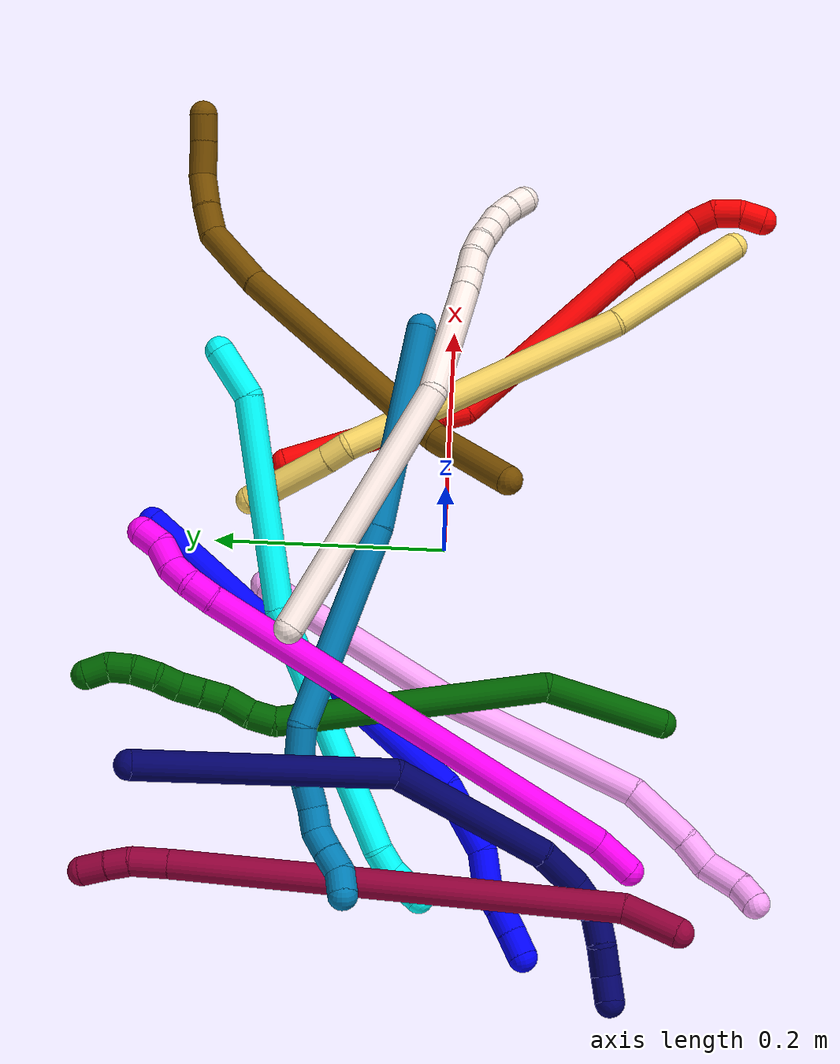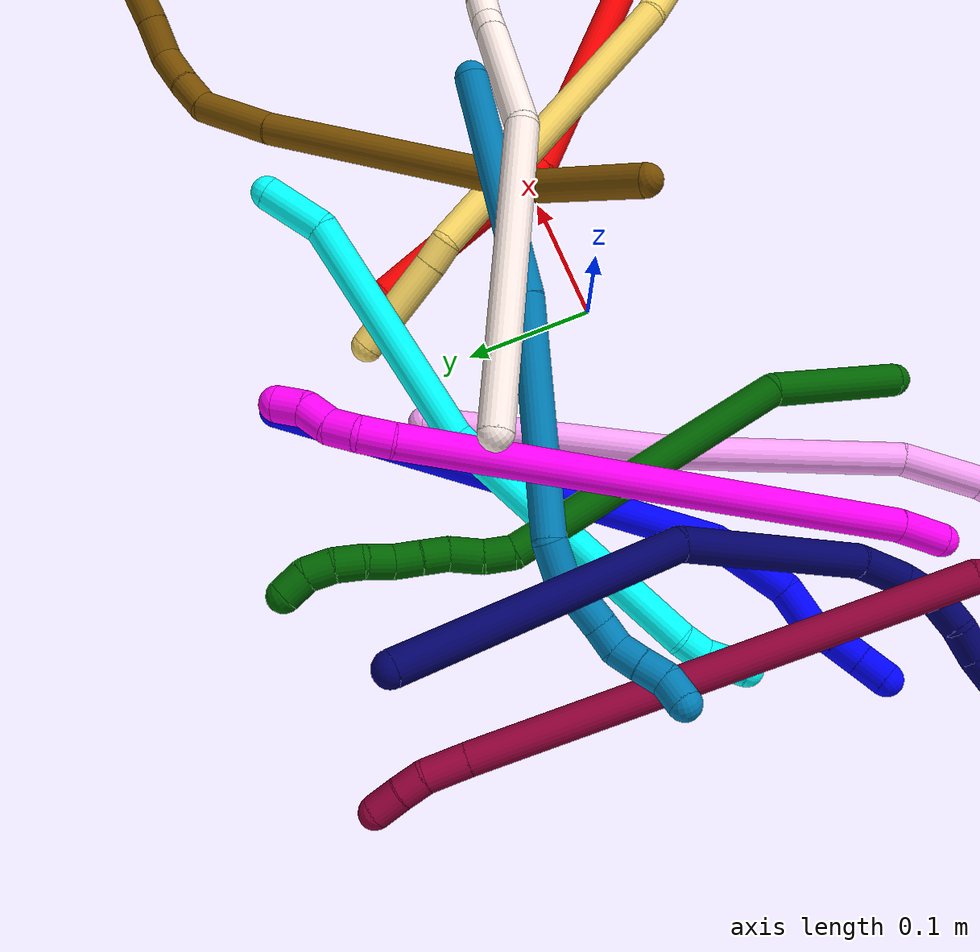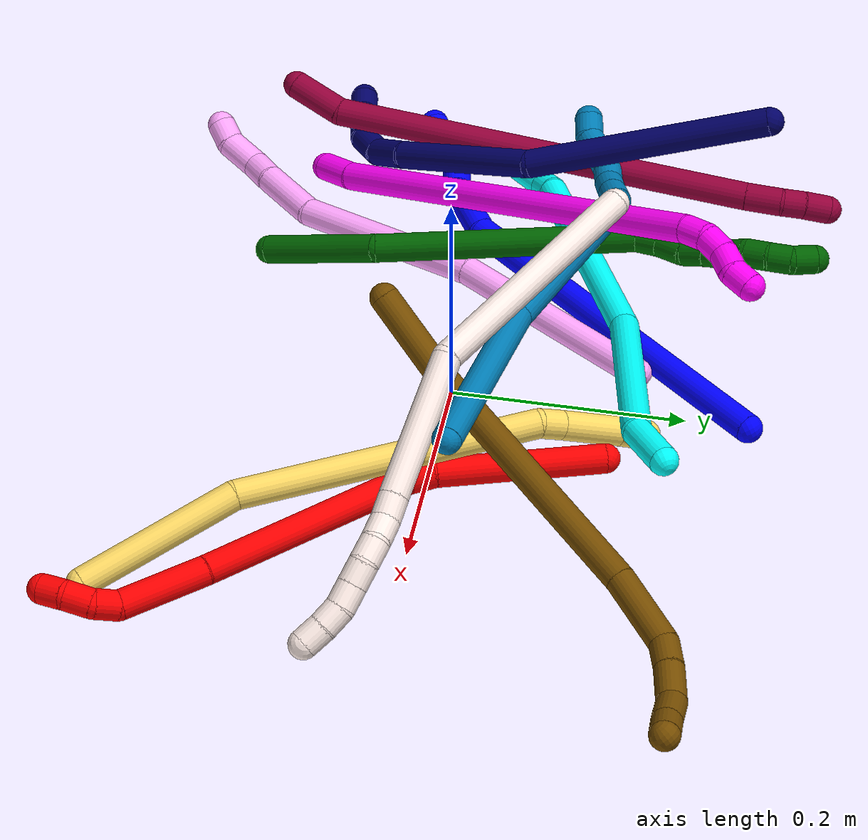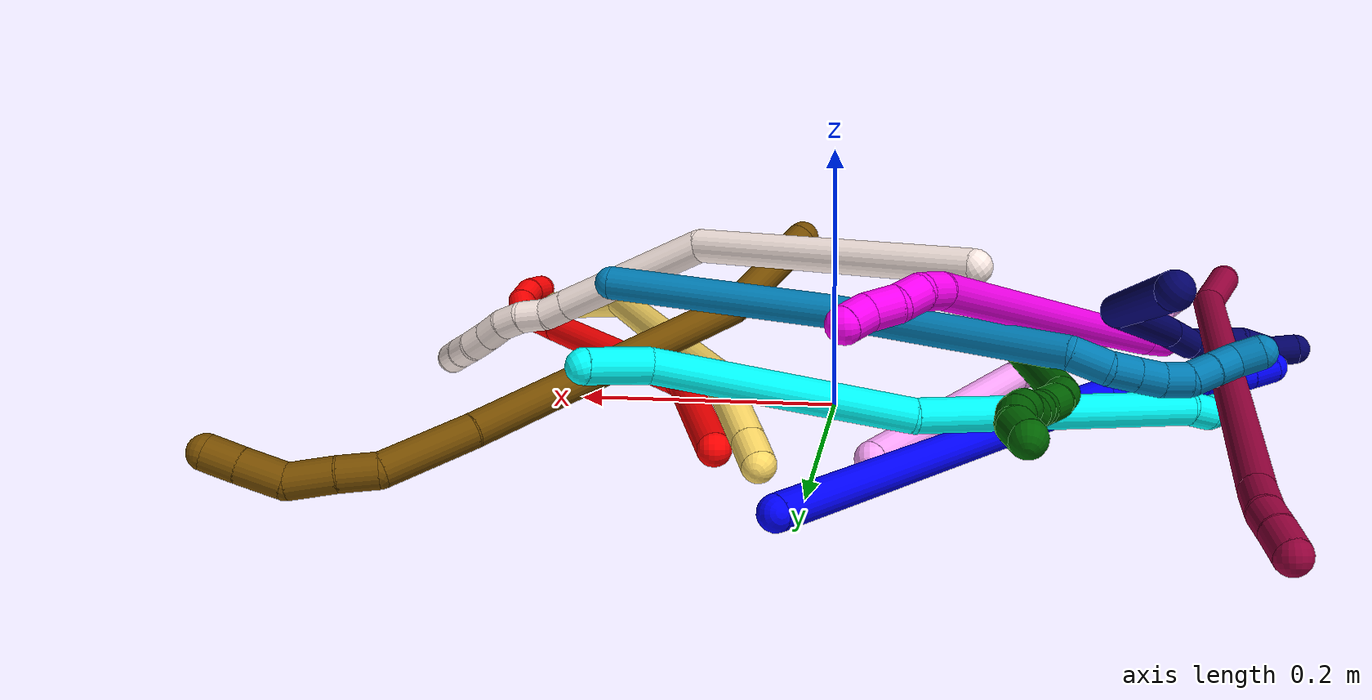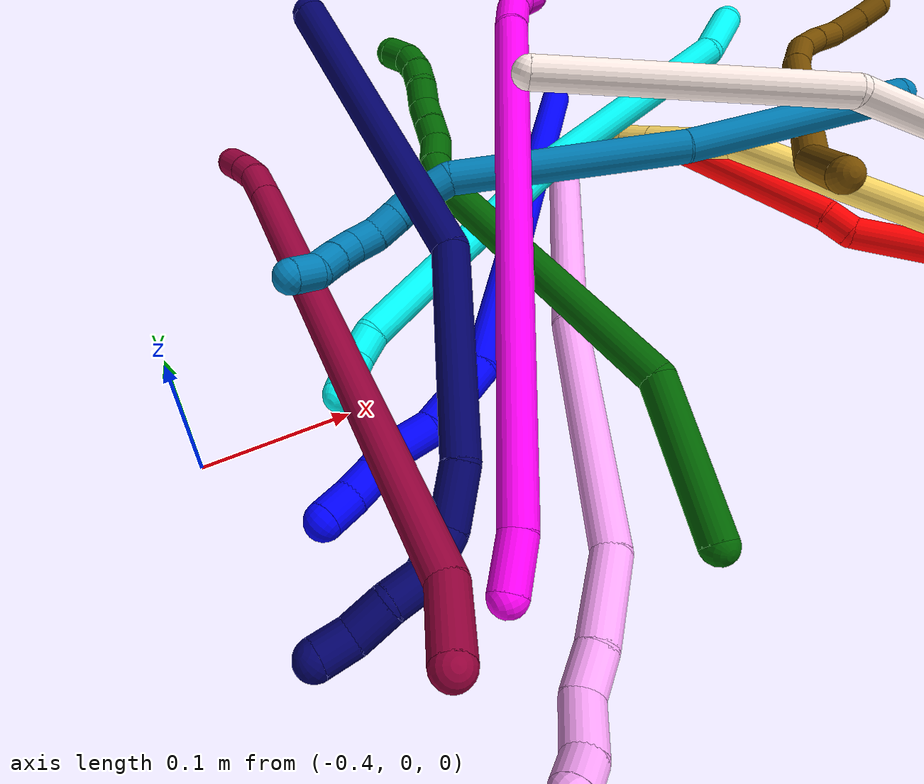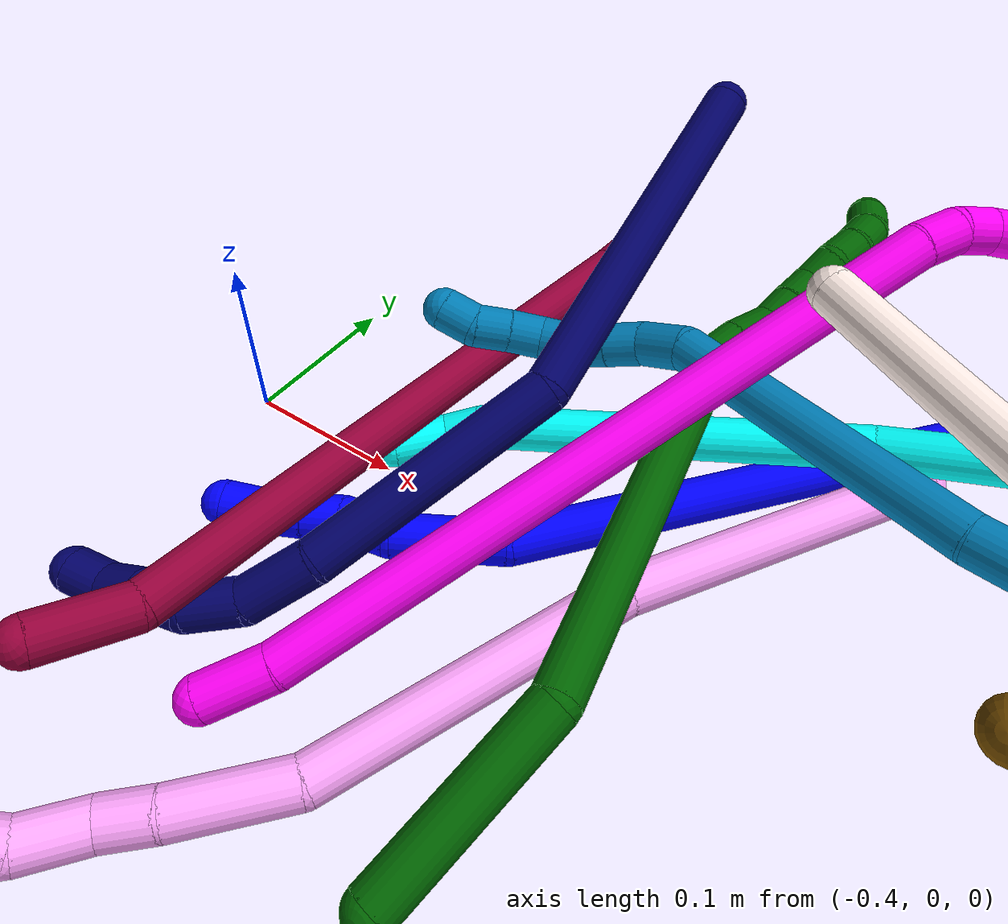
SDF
<sdf version="1.7">
 <world name="default">
  <plugin name="TubeGeneratorPlugin" filename="libtube_generator_plugin.so"/>
  <model name="photoneo_s_sensor">
   <static>1</static>
   <pose>0 0 2 1.57079 1.57079 3.14159</pose>
   <link name="link">
    <inertial><mass>0.1</mass></inertial>
    <sensor name="sensor" type="depth">
     <update_rate>30</update_rate>
     <camera>
      <horizontal_fov>1.22</horizontal_fov>
      <image><width>1920</width><height>1200</height><format>B8G8R8</format></image>
      <clip><near>0.1</near><far>4</far></clip>
      <depth_camera><output>points</output></depth_camera>
     </camera>
     <plugin name="camera_plugin" filename="libgazebo_ros_depth_camera.so">
      <baseline>0.2</baseline>
      <alwaysOn>1</alwaysOn>
      <updateRate>0.0</updateRate>
      <cameraName>camera_ir</cameraName>
      <imageTopicName>/camera/color/image_raw</imageTopicName>
      <cameraInfoTopicName>/camera/color/camera_info</cameraInfoTopicName>
      <depthImageTopicName>/camera/depth/image_raw</depthImageTopicName>
      <depthImageCameraInfoTopicName>/camera/depth/camera_info</depthImageCameraInfoTopicName>
      <pointCloudTopicName>/camera/depth/points</pointCloudTopicName>
      <frameName>fr_optical</frameName>
      <pointCloudCutoff>0.1</pointCloudCutoff>
      <pointCloudCutoffMax>2.0</pointCloudCutoffMax>
      <distortionK1>0</distortionK1>
      <distortionK2>0</distortionK2>
      <distortionK3>0</distortionK3>
      <distortionT1>0</distortionT1>
      <distortionT2>0</distortionT2>
      <CxPrime>0</CxPrime>
      <Cx>0</Cx>
      <Cy>0</Cy>
      <focalLength>0</focalLength>
      <hackBaseline>0</hackBaseline>
     </plugin>
    </sensor>
   </link>
  </model>
  <gravity>0 0 -9.8</gravity>
  <magnetic_field>6e-06 2.3e-05 -4.2e-05</magnetic_field>
  <atmosphere type="adiabatic"/>
  <physics name="default_physics" default="0" type="ode">
   <max_step_size>0.003</max_step_size>
   <real_time_factor>1</real_time_factor>
   <real_time_update_rate>1000</real_time_update_rate>
   <max_contacts>10000</max_contacts>
   <ode>
    <solver>
     <type>quick</type>
     <iters>100</iters>
     <sor>1.3</sor>
     <use_dynamic_moi_rescaling>0</use_dynamic_moi_rescaling>
    </solver>
    <constraints>
     <contact_max_correcting_vel>0</contact_max_correcting_vel>
     <contact_surface_layer>0.001</contact_surface_layer>
     <cfm>0</cfm>
     <erp>0.2</erp>
    </constraints>
   </ode>
  </physics>
  <scene><ambient>0.4 0.4 0.4 1</ambient><background>0.7 0.7 0.7 1</background><shadows>0</shadows></scene>
  <audio><device>default</device></audio>
  <spherical_coordinates>
   <surface_model>EARTH_WGS84</surface_model>
   <latitude_deg>0</latitude_deg>
   <longitude_deg>0</longitude_deg>
   <elevation>0</elevation>
   <heading_deg>0</heading_deg>
  </spherical_coordinates>
  <model name="bin">
   <static>1</static>
   <link name="bottom">
    <collision name="collision-bottom">
     <pose>0 0 -0.01 0 -0 0</pose>
     <geometry><box><size>0.8 0.6 0.02</size></box></geometry>
     <surface>
      <friction><ode><mu>100</mu><mu2>100</mu2></ode></friction>
      <contact><collide_bitmask>65535</collide_bitmask></contact>
     </surface>
    </collision>
   </link>
   <link name="west_wall">
    <collision name="collision-west_wall">
     <pose>-0.41 0 0.1 0 -0 0</pose>
     <geometry><box><size>0.02 0.6 0.2</size></box></geometry>
     <surface>
      <friction><ode><mu>100</mu><mu2>100</mu2></ode></friction>
      <contact><collide_bitmask>65535</collide_bitmask></contact>
     </surface>
    </collision>
   </link>
   <link name="east_wall">
    <collision name="collision-east_wall">
     <pose>0.41 0 0.1 0 -0 0</pose>
     <geometry><box><size>0.02 0.6 0.2</size></box></geometry>
     <surface>
      <friction><ode><mu>100</mu><mu2>100</mu2></ode></friction>
      <contact><collide_bitmask>65535</collide_bitmask></contact>
     </surface>
    </collision>
   </link>
   <link name="south_wall">
    <collision name="collision-south_wall">
     <pose>0 -0.31 0.1 0 -0 0</pose>
     <geometry><box><size>0.8 0.02 0.2</size></box></geometry>
     <surface>
      <friction><ode><mu>100</mu><mu2>100</mu2></ode></friction>
      <contact><collide_bitmask>65535</collide_bitmask></contact>
     </surface>
    </collision>
   </link>
   <link name="north_wall">
    <collision name="collision-north_wall">
     <pose>0 0.31 0.1 0 -0 0</pose>
     <geometry><box><size>0.8 0.02 0.2</size></box></geometry>
     <surface>
      <friction><ode><mu>100</mu><mu2>100</mu2></ode></friction>
      <contact><collide_bitmask>65535</collide_bitmask></contact>
     </surface>
    </collision>
   </link>
  </model>
  <model name="1">
   <static>0</static>
   <link name="1">
    <collision name="collision-cylinder-e_1_1_4">
     <pose>-0.141002 -0.074557 -0.063639 2.27736 -0.963302 -1.6957</pose>
     <geometry><cylinder><radius>0.0125</radius><length>0.343454</length></cylinder></geometry>
     <surface>
      <friction><ode><mu>1.16</mu><mu2>1.16</mu2><slip1>0</slip1><slip2>0</slip2></ode></friction>
      <contact><ode><kp>1e+06</kp><kd>1</kd><max_vel>0</max_vel><min_depth>0.001</min_depth></ode></contact>
     </surface>
    </collision>
    <visual name="visual-cylinder-e_1_1_4">
     <pose>-0.141002 -0.074557 -0.063639 2.27736 -0.963302 -1.6957</pose>
     <geometry><cylinder><radius>0.0125</radius><length>0.343454</length></cylinder></geometry>
     <material><ambient>0 0 1 1</ambient></material>
    </visual>
    <collision name="collision-cylinder-e_2_4_5">
     <pose>-0.310471 -0.160739 -0.128924 1.71139 -1.17959 -1.31317</pose>
     <geometry><cylinder><radius>0.0125</radius><length>0.061588</length></cylinder></geometry>
     <surface>
      <friction><ode><mu>1.16</mu><mu2>1.16</mu2><slip1>0</slip1><slip2>0</slip2></ode></friction>
      <contact><ode><kp>1e+06</kp><kd>1</kd><max_vel>0</max_vel><min_depth>0.001</min_depth></ode></contact>
     </surface>
    </collision>
    <visual name="visual-cylinder-e_2_4_5">
     <pose>-0.310471 -0.160739 -0.128924 1.71139 -1.17959 -1.31317</pose>
     <geometry><cylinder><radius>0.0125</radius><length>0.061588</length></cylinder></geometry>
     <material><ambient>0 0 1 1</ambient></material>
    </visual>
    <collision name="collision-cylinder-e_3_5_6">
     <pose>-0.353139 -0.175357 -0.126613 0.647427 -1.23471 -0.467666</pose>
     <geometry><cylinder><radius>0.0125</radius><length>0.030085</length></cylinder></geometry>
     <surface>
      <friction><ode><mu>1.16</mu><mu2>1.16</mu2><slip1>0</slip1><slip2>0</slip2></ode></friction>
      <contact><ode><kp>1e+06</kp><kd>1</kd><max_vel>0</max_vel><min_depth>0.001</min_depth></ode></contact>
     </surface>
    </collision>
    <visual name="visual-cylinder-e_3_5_6">
     <pose>-0.353139 -0.175357 -0.126613 0.647427 -1.23471 -0.467666</pose>
     <geometry><cylinder><radius>0.0125</radius><length>0.030085</length></cylinder></geometry>
     <material><ambient>0 0 1 1</ambient></material>
    </visual>
    <collision name="collision-cylinder-e_4_6_7">
     <pose>-0.377139 -0.18239 -0.123275 1.72293 -1.17558 -1.32026</pose>
     <geometry><cylinder><radius>0.0125</radius><length>0.021235</length></cylinder></geometry>
     <surface>
      <friction><ode><mu>1.16</mu><mu2>1.16</mu2><slip1>0</slip1><slip2>0</slip2></ode></friction>
      <contact><ode><kp>1e+06</kp><kd>1</kd><max_vel>0</max_vel><min_depth>0.001</min_depth></ode></contact>
     </surface>
    </collision>
    <visual name="visual-cylinder-e_4_6_7">
     <pose>-0.377139 -0.18239 -0.123275 1.72293 -1.17558 -1.32026</pose>
     <geometry><cylinder><radius>0.0125</radius><length>0.021235</length></cylinder></geometry>
     <material><ambient>0 0 1 1</ambient></material>
    </visual>
    <collision name="collision-cylinder-e_5_7_8">
     <pose>-0.396809 -0.190588 -0.123901 1.57237 -1.17216 -1.17362</pose>
     <geometry><cylinder><radius>0.0125</radius><length>0.02142</length></cylinder></geometry>
     <surface>
      <friction><ode><mu>1.16</mu><mu2>1.16</mu2><slip1>0</slip1><slip2>0</slip2></ode></friction>
      <contact><ode><kp>1e+06</kp><kd>1</kd><max_vel>0</max_vel><min_depth>0.001</min_depth></ode></contact>
     </surface>
    </collision>
    <visual name="visual-cylinder-e_5_7_8">
     <pose>-0.396809 -0.190588 -0.123901 1.57237 -1.17216 -1.17362</pose>
     <geometry><cylinder><radius>0.0125</radius><length>0.02142</length></cylinder></geometry>
     <material><ambient>0 0 1 1</ambient></material>
    </visual>
    <collision name="collision-cylinder-e_6_8_2">
     <pose>-0.416506 -0.199879 -0.123212 1.43602 -1.08563 -0.970006</pose>
     <geometry><cylinder><radius>0.0125</radius><length>0.022218</length></cylinder></geometry>
     <surface>
      <friction><ode><mu>1.16</mu><mu2>1.16</mu2><slip1>0</slip1><slip2>0</slip2></ode></friction>
      <contact><ode><kp>1e+06</kp><kd>1</kd><max_vel>0</max_vel><min_depth>0.001</min_depth></ode></contact>
     </surface>
    </collision>
    <visual name="visual-cylinder-e_6_8_2">
     <pose>-0.416506 -0.199879 -0.123212 1.43602 -1.08563 -0.970006</pose>
     <geometry><cylinder><radius>0.0125</radius><length>0.022218</length></cylinder></geometry>
     <material><ambient>0 0 1 1</ambient></material>
    </visual>
    <collision name="collision-sphere-2">
     <pose>-0.426333 -0.205013 -0.122515 0 -0 0</pose>
     <geometry><sphere><radius>0.0125</radius></sphere></geometry>
     <surface>
      <friction><ode><mu>1.16</mu><mu2>1.16</mu2><slip1>0</slip1><slip2>0</slip2></ode></friction>
      <contact><ode><kp>1e+06</kp><kd>1</kd><max_vel>0</max_vel><min_depth>0.001</min_depth></ode></contact>
     </surface>
    </collision>
    <visual name="visual-sphere-2">
     <pose>-0.426333 -0.205013 -0.122515 0 -0 0</pose>
     <geometry><sphere><radius>0.0125</radius></sphere></geometry>
     <material><ambient>0 0 1 1</ambient></material>
    </visual>
    <collision name="collision-sphere-4">
     <pose>-0.282003 -0.149113 -0.127279 0 -0 0</pose>
     <geometry><sphere><radius>0.0125</radius></sphere></geometry>
     <surface>
      <friction><ode><mu>1.16</mu><mu2>1.16</mu2><slip1>0</slip1><slip2>0</slip2></ode></friction>
      <contact><ode><kp>1e+06</kp><kd>1</kd><max_vel>0</max_vel><min_depth>0.001</min_depth></ode></contact>
     </surface>
    </collision>
    <visual name="visual-sphere-4">
     <pose>-0.282003 -0.149113 -0.127279 0 -0 0</pose>
     <geometry><sphere><radius>0.0125</radius></sphere></geometry>
     <material><ambient>0 0 1 1</ambient></material>
    </visual>
    <collision name="collision-sphere-1">
     <geometry><sphere><radius>0.0125</radius></sphere></geometry>
     <surface>
      <friction><ode><mu>1.16</mu><mu2>1.16</mu2><slip1>0</slip1><slip2>0</slip2></ode></friction>
      <contact><ode><kp>1e+06</kp><kd>1</kd><max_vel>0</max_vel><min_depth>0.001</min_depth></ode></contact>
     </surface>
    </collision>
    <visual name="visual-sphere-1">
     <geometry><sphere><radius>0.0125</radius></sphere></geometry>
     <material><ambient>0 0 1 1</ambient></material>
    </visual>
    <collision name="collision-sphere-8">
     <pose>-0.406679 -0.194745 -0.123908 0 -0 0</pose>
     <geometry><sphere><radius>0.0125</radius></sphere></geometry>
     <surface>
      <friction><ode><mu>1.16</mu><mu2>1.16</mu2><slip1>0</slip1><slip2>0</slip2></ode></friction>
      <contact><ode><kp>1e+06</kp><kd>1</kd><max_vel>0</max_vel><min_depth>0.001</min_depth></ode></contact>
     </surface>
    </collision>
    <visual name="visual-sphere-8">
     <pose>-0.406679 -0.194745 -0.123908 0 -0 0</pose>
     <geometry><sphere><radius>0.0125</radius></sphere></geometry>
     <material><ambient>0 0 1 1</ambient></material>
    </visual>
    <collision name="collision-sphere-5">
     <pose>-0.338938 -0.172365 -0.13057 0 -0 0</pose>
     <geometry><sphere><radius>0.0125</radius></sphere></geometry>
     <surface>
      <friction><ode><mu>1.16</mu><mu2>1.16</mu2><slip1>0</slip1><slip2>0</slip2></ode></friction>
      <contact><ode><kp>1e+06</kp><kd>1</kd><max_vel>0</max_vel><min_depth>0.001</min_depth></ode></contact>
     </surface>
    </collision>
    <visual name="visual-sphere-5">
     <pose>-0.338938 -0.172365 -0.13057 0 -0 0</pose>
     <geometry><sphere><radius>0.0125</radius></sphere></geometry>
     <material><ambient>0 0 1 1</ambient></material>
    </visual>
    <collision name="collision-sphere-6">
     <pose>-0.36734 -0.17835 -0.122656 0 -0 0</pose>
     <geometry><sphere><radius>0.0125</radius></sphere></geometry>
     <surface>
      <friction><ode><mu>1.16</mu><mu2>1.16</mu2><slip1>0</slip1><slip2>0</slip2></ode></friction>
      <contact><ode><kp>1e+06</kp><kd>1</kd><max_vel>0</max_vel><min_depth>0.001</min_depth></ode></contact>
     </surface>
    </collision>
    <visual name="visual-sphere-6">
     <pose>-0.36734 -0.17835 -0.122656 0 -0 0</pose>
     <geometry><sphere><radius>0.0125</radius></sphere></geometry>
     <material><ambient>0 0 1 1</ambient></material>
    </visual>
    <collision name="collision-sphere-7">
     <pose>-0.386939 -0.186431 -0.123895 0 -0 0</pose>
     <geometry><sphere><radius>0.0125</radius></sphere></geometry>
     <surface>
      <friction><ode><mu>1.16</mu><mu2>1.16</mu2><slip1>0</slip1><slip2>0</slip2></ode></friction>
      <contact><ode><kp>1e+06</kp><kd>1</kd><max_vel>0</max_vel><min_depth>0.001</min_depth></ode></contact>
     </surface>
    </collision>
    <visual name="visual-sphere-7">
     <pose>-0.386939 -0.186431 -0.123895 0 -0 0</pose>
     <geometry><sphere><radius>0.0125</radius></sphere></geometry>
     <material><ambient>0 0 1 1</ambient></material>
    </visual>
    <inertial>
     <pose>-0.20787 -0.106357 -0.083232 0 -0 0</pose>
     <mass>0.5</mass>
     <inertia>
      <ixx>-0.002201</ixx>
      <ixy>0</ixy>
      <ixz>0</ixz>
      <iyy>0.000454</iyy>
      <iyz>0</iyz>
      <izz>0.004284</izz>
     </inertia>
    </inertial>
   </link>
   <pose>0.011945 0.253267 0.01149 -1.1964 -0.315944 0.352663</pose>
  </model>
  <model name="2">
   <static>0</static>
   <link name="2">
    <collision name="collision-cylinder-e_1_1_4">
     <pose>0.041332 -0.05688 0.00931 1.40856 0.622124 0.533302</pose>
     <geometry><cylinder><radius>0.0125</radius><length>0.141849</length></cylinder></geometry>
     <surface>
      <friction><ode><mu>1.16</mu><mu2>1.16</mu2><slip1>0</slip1><slip2>0</slip2></ode></friction>
      <contact><ode><kp>1e+06</kp><kd>1</kd><max_vel>0</max_vel><min_depth>0.001</min_depth></ode></contact>
     </surface>
    </collision>
    <visual name="visual-cylinder-e_1_1_4">
     <pose>0.041332 -0.05688 0.00931 1.40856 0.622124 0.533302</pose>
     <geometry><cylinder><radius>0.0125</radius><length>0.141849</length></cylinder></geometry>
     <material><ambient>1 0 0 1</ambient></material>
    </visual>
    <collision name="collision-cylinder-e_2_4_5">
     <pose>0.091303 -0.121326 0.020123 1.3746 0.841856 0.704294</pose>
     <geometry><cylinder><radius>0.0125</radius><length>0.023164</length></cylinder></geometry>
     <surface>
      <friction><ode><mu>1.16</mu><mu2>1.16</mu2><slip1>0</slip1><slip2>0</slip2></ode></friction>
      <contact><ode><kp>1e+06</kp><kd>1</kd><max_vel>0</max_vel><min_depth>0.001</min_depth></ode></contact>
     </surface>
    </collision>
    <visual name="visual-cylinder-e_2_4_5">
     <pose>0.091303 -0.121326 0.020123 1.3746 0.841856 0.704294</pose>
     <geometry><cylinder><radius>0.0125</radius><length>0.023164</length></cylinder></geometry>
     <material><ambient>1 0 0 1</ambient></material>
    </visual>
    <collision name="collision-cylinder-e_3_5_6">
     <pose>0.150244 -0.193085 0.074277 0.883868 0.544736 0.262785</pose>
     <geometry><cylinder><radius>0.0125</radius><length>0.194146</length></cylinder></geometry>
     <surface>
      <friction><ode><mu>1.16</mu><mu2>1.16</mu2><slip1>0</slip1><slip2>0</slip2></ode></friction>
      <contact><ode><kp>1e+06</kp><kd>1</kd><max_vel>0</max_vel><min_depth>0.001</min_depth></ode></contact>
     </surface>
    </collision>
    <visual name="visual-cylinder-e_3_5_6">
     <pose>0.150244 -0.193085 0.074277 0.883868 0.544736 0.262785</pose>
     <geometry><cylinder><radius>0.0125</radius><length>0.194146</length></cylinder></geometry>
     <material><ambient>1 0 0 1</ambient></material>
    </visual>
    <collision name="collision-cylinder-e_4_6_7">
     <pose>0.222505 -0.282916 0.14468 0.965166 0.613512 0.328897</pose>
     <geometry><cylinder><radius>0.0125</radius><length>0.07628</length></cylinder></geometry>
     <surface>
      <friction><ode><mu>1.16</mu><mu2>1.16</mu2><slip1>0</slip1><slip2>0</slip2></ode></friction>
      <contact><ode><kp>1e+06</kp><kd>1</kd><max_vel>0</max_vel><min_depth>0.001</min_depth></ode></contact>
     </surface>
    </collision>
    <visual name="visual-cylinder-e_4_6_7">
     <pose>0.222505 -0.282916 0.14468 0.965166 0.613512 0.328897</pose>
     <geometry><cylinder><radius>0.0125</radius><length>0.07628</length></cylinder></geometry>
     <material><ambient>1 0 0 1</ambient></material>
    </visual>
    <collision name="collision-cylinder-e_5_7_8">
     <pose>0.248017 -0.318354 0.164455 1.36734 0.341219 0.278913</pose>
     <geometry><cylinder><radius>0.0125</radius><length>0.021236</length></cylinder></geometry>
     <surface>
      <friction><ode><mu>1.16</mu><mu2>1.16</mu2><slip1>0</slip1><slip2>0</slip2></ode></friction>
      <contact><ode><kp>1e+06</kp><kd>1</kd><max_vel>0</max_vel><min_depth>0.001</min_depth></ode></contact>
     </surface>
    </collision>
    <visual name="visual-cylinder-e_5_7_8">
     <pose>0.248017 -0.318354 0.164455 1.36734 0.341219 0.278913</pose>
     <geometry><cylinder><radius>0.0125</radius><length>0.021236</length></cylinder></geometry>
     <material><ambient>1 0 0 1</ambient></material>
    </visual>
    <collision name="collision-cylinder-e_6_8_9">
     <pose>0.256371 -0.338165 0.163558 1.85441 0.431404 0.568374</pose>
     <geometry><cylinder><radius>0.0125</radius><length>0.02296</length></cylinder></geometry>
     <surface>
      <friction><ode><mu>1.16</mu><mu2>1.16</mu2><slip1>0</slip1><slip2>0</slip2></ode></friction>
      <contact><ode><kp>1e+06</kp><kd>1</kd><max_vel>0</max_vel><min_depth>0.001</min_depth></ode></contact>
     </surface>
    </collision>
    <visual name="visual-cylinder-e_6_8_9">
     <pose>0.256371 -0.338165 0.163558 1.85441 0.431404 0.568374</pose>
     <geometry><cylinder><radius>0.0125</radius><length>0.02296</length></cylinder></geometry>
     <material><ambient>1 0 0 1</ambient></material>
    </visual>
    <collision name="collision-cylinder-e_7_9_2">
     <pose>0.267262 -0.354966 0.156114 2.15876 0.64114 1.11051</pose>
     <geometry><cylinder><radius>0.0125</radius><length>0.020366</length></cylinder></geometry>
     <surface>
      <friction><ode><mu>1.16</mu><mu2>1.16</mu2><slip1>0</slip1><slip2>0</slip2></ode></friction>
      <contact><ode><kp>1e+06</kp><kd>1</kd><max_vel>0</max_vel><min_depth>0.001</min_depth></ode></contact>
     </surface>
    </collision>
    <visual name="visual-cylinder-e_7_9_2">
     <pose>0.267262 -0.354966 0.156114 2.15876 0.64114 1.11051</pose>
     <geometry><cylinder><radius>0.0125</radius><length>0.020366</length></cylinder></geometry>
     <material><ambient>1 0 0 1</ambient></material>
    </visual>
    <collision name="collision-sphere-2">
     <pose>0.273352 -0.361757 0.151587 0 -0 0</pose>
     <geometry><sphere><radius>0.0125</radius></sphere></geometry>
     <surface>
      <friction><ode><mu>1.16</mu><mu2>1.16</mu2><slip1>0</slip1><slip2>0</slip2></ode></friction>
      <contact><ode><kp>1e+06</kp><kd>1</kd><max_vel>0</max_vel><min_depth>0.001</min_depth></ode></contact>
     </surface>
    </collision>
    <visual name="visual-sphere-2">
     <pose>0.273352 -0.361757 0.151587 0 -0 0</pose>
     <geometry><sphere><radius>0.0125</radius></sphere></geometry>
     <material><ambient>1 0 0 1</ambient></material>
    </visual>
    <collision name="collision-sphere-9">
     <pose>0.261171 -0.348176 0.16064 0 -0 0</pose>
     <geometry><sphere><radius>0.0125</radius></sphere></geometry>
     <surface>
      <friction><ode><mu>1.16</mu><mu2>1.16</mu2><slip1>0</slip1><slip2>0</slip2></ode></friction>
      <contact><ode><kp>1e+06</kp><kd>1</kd><max_vel>0</max_vel><min_depth>0.001</min_depth></ode></contact>
     </surface>
    </collision>
    <visual name="visual-sphere-9">
     <pose>0.261171 -0.348176 0.16064 0 -0 0</pose>
     <geometry><sphere><radius>0.0125</radius></sphere></geometry>
     <material><ambient>1 0 0 1</ambient></material>
    </visual>
    <collision name="collision-sphere-4">
     <pose>0.082665 -0.113759 0.018619 0 -0 0</pose>
     <geometry><sphere><radius>0.0125</radius></sphere></geometry>
     <surface>
      <friction><ode><mu>1.16</mu><mu2>1.16</mu2><slip1>0</slip1><slip2>0</slip2></ode></friction>
      <contact><ode><kp>1e+06</kp><kd>1</kd><max_vel>0</max_vel><min_depth>0.001</min_depth></ode></contact>
     </surface>
    </collision>
    <visual name="visual-sphere-4">
     <pose>0.082665 -0.113759 0.018619 0 -0 0</pose>
     <geometry><sphere><radius>0.0125</radius></sphere></geometry>
     <material><ambient>1 0 0 1</ambient></material>
    </visual>
    <collision name="collision-sphere-1">
     <geometry><sphere><radius>0.0125</radius></sphere></geometry>
     <surface>
      <friction><ode><mu>1.16</mu><mu2>1.16</mu2><slip1>0</slip1><slip2>0</slip2></ode></friction>
      <contact><ode><kp>1e+06</kp><kd>1</kd><max_vel>0</max_vel><min_depth>0.001</min_depth></ode></contact>
     </surface>
    </collision>
    <visual name="visual-sphere-1">
     <geometry><sphere><radius>0.0125</radius></sphere></geometry>
     <material><ambient>1 0 0 1</ambient></material>
    </visual>
    <collision name="collision-sphere-8">
     <pose>0.25157 -0.328153 0.166476 0 -0 0</pose>
     <geometry><sphere><radius>0.0125</radius></sphere></geometry>
     <surface>
      <friction><ode><mu>1.16</mu><mu2>1.16</mu2><slip1>0</slip1><slip2>0</slip2></ode></friction>
      <contact><ode><kp>1e+06</kp><kd>1</kd><max_vel>0</max_vel><min_depth>0.001</min_depth></ode></contact>
     </surface>
    </collision>
    <visual name="visual-sphere-8">
     <pose>0.25157 -0.328153 0.166476 0 -0 0</pose>
     <geometry><sphere><radius>0.0125</radius></sphere></geometry>
     <material><ambient>1 0 0 1</ambient></material>
    </visual>
    <collision name="collision-sphere-5">
     <pose>0.099942 -0.128892 0.021627 0 -0 0</pose>
     <geometry><sphere><radius>0.0125</radius></sphere></geometry>
     <surface>
      <friction><ode><mu>1.16</mu><mu2>1.16</mu2><slip1>0</slip1><slip2>0</slip2></ode></friction>
      <contact><ode><kp>1e+06</kp><kd>1</kd><max_vel>0</max_vel><min_depth>0.001</min_depth></ode></contact>
     </surface>
    </collision>
    <visual name="visual-sphere-5">
     <pose>0.099942 -0.128892 0.021627 0 -0 0</pose>
     <geometry><sphere><radius>0.0125</radius></sphere></geometry>
     <material><ambient>1 0 0 1</ambient></material>
    </visual>
    <collision name="collision-sphere-6">
     <pose>0.200547 -0.257278 0.126928 0 -0 0</pose>
     <geometry><sphere><radius>0.0125</radius></sphere></geometry>
     <surface>
      <friction><ode><mu>1.16</mu><mu2>1.16</mu2><slip1>0</slip1><slip2>0</slip2></ode></friction>
      <contact><ode><kp>1e+06</kp><kd>1</kd><max_vel>0</max_vel><min_depth>0.001</min_depth></ode></contact>
     </surface>
    </collision>
    <visual name="visual-sphere-6">
     <pose>0.200547 -0.257278 0.126928 0 -0 0</pose>
     <geometry><sphere><radius>0.0125</radius></sphere></geometry>
     <material><ambient>1 0 0 1</ambient></material>
    </visual>
    <collision name="collision-sphere-7">
     <pose>0.244464 -0.308554 0.162433 0 -0 0</pose>
     <geometry><sphere><radius>0.0125</radius></sphere></geometry>
     <surface>
      <friction><ode><mu>1.16</mu><mu2>1.16</mu2><slip1>0</slip1><slip2>0</slip2></ode></friction>
      <contact><ode><kp>1e+06</kp><kd>1</kd><max_vel>0</max_vel><min_depth>0.001</min_depth></ode></contact>
     </surface>
    </collision>
    <visual name="visual-sphere-7">
     <pose>0.244464 -0.308554 0.162433 0 -0 0</pose>
     <geometry><sphere><radius>0.0125</radius></sphere></geometry>
     <material><ambient>1 0 0 1</ambient></material>
    </visual>
    <inertial>
     <pose>0.141432 -0.1834 0.075341 0 -0 0</pose>
     <mass>0.5</mass>
     <inertia><ixx>0.000989</ixx><ixy>0</ixy><ixz>0</ixz><iyy>0.0008</iyy><iyz>0</iyz><izz>0.000159</izz></inertia>
    </inertial>
   </link>
   <pose>0.069951 0.142103 0.011466 -1.49555 0.915783 -1.30288</pose>
  </model>
  <model name="3">
   <static>0</static>
   <link name="3">
    <collision name="collision-cylinder-e_1_1_4">
     <pose>-0.007433 0.003183 -0.021824 -2.99677 -0.325066 2.30865</pose>
     <geometry><cylinder><radius>0.0125</radius><length>0.046548</length></cylinder></geometry>
     <surface>
      <friction><ode><mu>1.16</mu><mu2>1.16</mu2><slip1>0</slip1><slip2>0</slip2></ode></friction>
      <contact><ode><kp>1e+06</kp><kd>1</kd><max_vel>0</max_vel><min_depth>0.001</min_depth></ode></contact>
     </surface>
    </collision>
    <visual name="visual-cylinder-e_1_1_4">
     <pose>-0.007433 0.003183 -0.021824 -2.99677 -0.325066 2.30865</pose>
     <geometry><cylinder><radius>0.0125</radius><length>0.046548</length></cylinder></geometry>
     <material><ambient>0.003922 1 0.996078 1</ambient></material>
    </visual>
    <collision name="collision-cylinder-e_2_4_5">
     <pose>-0.057886 -0.016118 -0.120758 2.85788 -0.491718 -2.10676</pose>
     <geometry><cylinder><radius>0.0125</radius><length>0.182231</length></cylinder></geometry>
     <surface>
      <friction><ode><mu>1.16</mu><mu2>1.16</mu2><slip1>0</slip1><slip2>0</slip2></ode></friction>
      <contact><ode><kp>1e+06</kp><kd>1</kd><max_vel>0</max_vel><min_depth>0.001</min_depth></ode></contact>
     </surface>
    </collision>
    <visual name="visual-cylinder-e_2_4_5">
     <pose>-0.057886 -0.016118 -0.120758 2.85788 -0.491718 -2.10676</pose>
     <geometry><cylinder><radius>0.0125</radius><length>0.182231</length></cylinder></geometry>
     <material><ambient>0.003922 1 0.996078 1</ambient></material>
    </visual>
    <collision name="collision-cylinder-e_3_5_6">
     <pose>-0.134194 -0.043418 -0.301417 3.09512 -0.310725 -2.84695</pose>
     <geometry><cylinder><radius>0.0125</radius><length>0.21775</length></cylinder></geometry>
     <surface>
      <friction><ode><mu>1.16</mu><mu2>1.16</mu2><slip1>0</slip1><slip2>0</slip2></ode></friction>
      <contact><ode><kp>1e+06</kp><kd>1</kd><max_vel>0</max_vel><min_depth>0.001</min_depth></ode></contact>
     </surface>
    </collision>
    <visual name="visual-cylinder-e_3_5_6">
     <pose>-0.134194 -0.043418 -0.301417 3.09512 -0.310725 -2.84695</pose>
     <geometry><cylinder><radius>0.0125</radius><length>0.21775</length></cylinder></geometry>
     <material><ambient>0.003922 1 0.996078 1</ambient></material>
    </visual>
    <collision name="collision-cylinder-e_4_6_7">
     <pose>-0.172712 -0.046569 -0.414122 -2.96175 -0.512023 2.47813</pose>
     <geometry><cylinder><radius>0.0125</radius><length>0.021348</length></cylinder></geometry>
     <surface>
      <friction><ode><mu>1.16</mu><mu2>1.16</mu2><slip1>0</slip1><slip2>0</slip2></ode></friction>
      <contact><ode><kp>1e+06</kp><kd>1</kd><max_vel>0</max_vel><min_depth>0.001</min_depth></ode></contact>
     </surface>
    </collision>
    <visual name="visual-cylinder-e_4_6_7">
     <pose>-0.172712 -0.046569 -0.414122 -2.96175 -0.512023 2.47813</pose>
     <geometry><cylinder><radius>0.0125</radius><length>0.021348</length></cylinder></geometry>
     <material><ambient>0.003922 1 0.996078 1</ambient></material>
    </visual>
    <collision name="collision-cylinder-e_5_7_2">
     <pose>-0.180497 -0.039467 -0.438172 -2.79157 -0.159778 0.850306</pose>
     <geometry><cylinder><radius>0.0125</radius><length>0.032122</length></cylinder></geometry>
     <surface>
      <friction><ode><mu>1.16</mu><mu2>1.16</mu2><slip1>0</slip1><slip2>0</slip2></ode></friction>
      <contact><ode><kp>1e+06</kp><kd>1</kd><max_vel>0</max_vel><min_depth>0.001</min_depth></ode></contact>
     </surface>
    </collision>
    <visual name="visual-cylinder-e_5_7_2">
     <pose>-0.180497 -0.039467 -0.438172 -2.79157 -0.159778 0.850306</pose>
     <geometry><cylinder><radius>0.0125</radius><length>0.032122</length></cylinder></geometry>
     <material><ambient>0.003922 1 0.996078 1</ambient></material>
    </visual>
    <collision name="collision-sphere-2">
     <pose>-0.183052 -0.03403 -0.453067 0 -0 0</pose>
     <geometry><sphere><radius>0.0125</radius></sphere></geometry>
     <surface>
      <friction><ode><mu>1.16</mu><mu2>1.16</mu2><slip1>0</slip1><slip2>0</slip2></ode></friction>
      <contact><ode><kp>1e+06</kp><kd>1</kd><max_vel>0</max_vel><min_depth>0.001</min_depth></ode></contact>
     </surface>
    </collision>
    <visual name="visual-sphere-2">
     <pose>-0.183052 -0.03403 -0.453067 0 -0 0</pose>
     <geometry><sphere><radius>0.0125</radius></sphere></geometry>
     <material><ambient>0.003922 1 0.996078 1</ambient></material>
    </visual>
    <collision name="collision-sphere-7">
     <pose>-0.177941 -0.044905 -0.423277 0 -0 0</pose>
     <geometry><sphere><radius>0.0125</radius></sphere></geometry>
     <surface>
      <friction><ode><mu>1.16</mu><mu2>1.16</mu2><slip1>0</slip1><slip2>0</slip2></ode></friction>
      <contact><ode><kp>1e+06</kp><kd>1</kd><max_vel>0</max_vel><min_depth>0.001</min_depth></ode></contact>
     </surface>
    </collision>
    <visual name="visual-sphere-7">
     <pose>-0.177941 -0.044905 -0.423277 0 -0 0</pose>
     <geometry><sphere><radius>0.0125</radius></sphere></geometry>
     <material><ambient>0.003922 1 0.996078 1</ambient></material>
    </visual>
    <collision name="collision-sphere-6">
     <pose>-0.167482 -0.048234 -0.404967 0 -0 0</pose>
     <geometry><sphere><radius>0.0125</radius></sphere></geometry>
     <surface>
      <friction><ode><mu>1.16</mu><mu2>1.16</mu2><slip1>0</slip1><slip2>0</slip2></ode></friction>
      <contact><ode><kp>1e+06</kp><kd>1</kd><max_vel>0</max_vel><min_depth>0.001</min_depth></ode></contact>
     </surface>
    </collision>
    <visual name="visual-sphere-6">
     <pose>-0.167482 -0.048234 -0.404967 0 -0 0</pose>
     <geometry><sphere><radius>0.0125</radius></sphere></geometry>
     <material><ambient>0.003922 1 0.996078 1</ambient></material>
    </visual>
    <collision name="collision-sphere-5">
     <pose>-0.100905 -0.038602 -0.197868 0 -0 0</pose>
     <geometry><sphere><radius>0.0125</radius></sphere></geometry>
     <surface>
      <friction><ode><mu>1.16</mu><mu2>1.16</mu2><slip1>0</slip1><slip2>0</slip2></ode></friction>
      <contact><ode><kp>1e+06</kp><kd>1</kd><max_vel>0</max_vel><min_depth>0.001</min_depth></ode></contact>
     </surface>
    </collision>
    <visual name="visual-sphere-5">
     <pose>-0.100905 -0.038602 -0.197868 0 -0 0</pose>
     <geometry><sphere><radius>0.0125</radius></sphere></geometry>
     <material><ambient>0.003922 1 0.996078 1</ambient></material>
    </visual>
    <collision name="collision-sphere-1">
     <geometry><sphere><radius>0.0125</radius></sphere></geometry>
     <surface>
      <friction><ode><mu>1.16</mu><mu2>1.16</mu2><slip1>0</slip1><slip2>0</slip2></ode></friction>
      <contact><ode><kp>1e+06</kp><kd>1</kd><max_vel>0</max_vel><min_depth>0.001</min_depth></ode></contact>
     </surface>
    </collision>
    <visual name="visual-sphere-1">
     <geometry><sphere><radius>0.0125</radius></sphere></geometry>
     <material><ambient>0.003922 1 0.996078 1</ambient></material>
    </visual>
    <collision name="collision-sphere-4">
     <pose>-0.014866 0.006366 -0.043649 0 -0 0</pose>
     <geometry><sphere><radius>0.0125</radius></sphere></geometry>
     <surface>
      <friction><ode><mu>1.16</mu><mu2>1.16</mu2><slip1>0</slip1><slip2>0</slip2></ode></friction>
      <contact><ode><kp>1e+06</kp><kd>1</kd><max_vel>0</max_vel><min_depth>0.001</min_depth></ode></contact>
     </surface>
    </collision>
    <visual name="visual-sphere-4">
     <pose>-0.014866 0.006366 -0.043649 0 -0 0</pose>
     <geometry><sphere><radius>0.0125</radius></sphere></geometry>
     <material><ambient>0.003922 1 0.996078 1</ambient></material>
    </visual>
    <inertial>
     <pose>-0.099201 -0.02901 -0.223142 0 -0 0</pose>
     <mass>0.5</mass>
     <inertia>
      <ixx>-0.001658</ixx>
      <ixy>0</ixy>
      <ixz>0</ixz>
      <iyy>0.00053</iyy>
      <iyz>0</iyz>
      <izz>0.000638</izz>
     </inertia>
    </inertial>
   </link>
   <pose>0.144261 0.197906 0.085389 -2.36749 -1.27249 -0.244764</pose>
  </model>
  <model name="4">
   <static>0</static>
   <link name="4">
    <collision name="collision-cylinder-e_1_1_4">
     <pose>-0.02478 -0.073297 0.055348 0.924022 -0.263522 -0.131796</pose>
     <geometry><cylinder><radius>0.0125</radius><length>0.190262</length></cylinder></geometry>
     <surface>
      <friction><ode><mu>1.16</mu><mu2>1.16</mu2><slip1>0</slip1><slip2>0</slip2></ode></friction>
      <contact><ode><kp>1e+06</kp><kd>1</kd><max_vel>0</max_vel><min_depth>0.001</min_depth></ode></contact>
     </surface>
    </collision>
    <visual name="visual-cylinder-e_1_1_4">
     <pose>-0.02478 -0.073297 0.055348 0.924022 -0.263522 -0.131796</pose>
     <geometry><cylinder><radius>0.0125</radius><length>0.190262</length></cylinder></geometry>
     <material><ambient>1 0.65098 0.996078 1</ambient></material>
    </visual>
    <collision name="collision-cylinder-e_2_4_5">
     <pose>-0.058905 -0.217494 0.15712 0.991083 -0.109832 -0.059409</pose>
     <geometry><cylinder><radius>0.0125</radius><length>0.170521</length></cylinder></geometry>
     <surface>
      <friction><ode><mu>1.16</mu><mu2>1.16</mu2><slip1>0</slip1><slip2>0</slip2></ode></friction>
      <contact><ode><kp>1e+06</kp><kd>1</kd><max_vel>0</max_vel><min_depth>0.001</min_depth></ode></contact>
     </surface>
    </collision>
    <visual name="visual-cylinder-e_2_4_5">
     <pose>-0.058905 -0.217494 0.15712 0.991083 -0.109832 -0.059409</pose>
     <geometry><cylinder><radius>0.0125</radius><length>0.170521</length></cylinder></geometry>
     <material><ambient>1 0.65098 0.996078 1</ambient></material>
    </visual>
    <collision name="collision-cylinder-e_3_5_6">
     <pose>-0.080591 -0.310912 0.217741 1.0082 -0.4341 -0.242111</pose>
     <geometry><cylinder><radius>0.0125</radius><length>0.058681</length></cylinder></geometry>
     <surface>
      <friction><ode><mu>1.16</mu><mu2>1.16</mu2><slip1>0</slip1><slip2>0</slip2></ode></friction>
      <contact><ode><kp>1e+06</kp><kd>1</kd><max_vel>0</max_vel><min_depth>0.001</min_depth></ode></contact>
     </surface>
    </collision>
    <visual name="visual-cylinder-e_3_5_6">
     <pose>-0.080591 -0.310912 0.217741 1.0082 -0.4341 -0.242111</pose>
     <geometry><cylinder><radius>0.0125</radius><length>0.058681</length></cylinder></geometry>
     <material><ambient>1 0.65098 0.996078 1</ambient></material>
    </visual>
    <collision name="collision-cylinder-e_4_6_7">
     <pose>-0.099641 -0.344294 0.236633 1.16301 -0.515671 -0.343265</pose>
     <geometry><cylinder><radius>0.0125</radius><length>0.027211</length></cylinder></geometry>
     <surface>
      <friction><ode><mu>1.16</mu><mu2>1.16</mu2><slip1>0</slip1><slip2>0</slip2></ode></friction>
      <contact><ode><kp>1e+06</kp><kd>1</kd><max_vel>0</max_vel><min_depth>0.001</min_depth></ode></contact>
     </surface>
    </collision>
    <visual name="visual-cylinder-e_4_6_7">
     <pose>-0.099641 -0.344294 0.236633 1.16301 -0.515671 -0.343265</pose>
     <geometry><cylinder><radius>0.0125</radius><length>0.027211</length></cylinder></geometry>
     <material><ambient>1 0.65098 0.996078 1</ambient></material>
    </visual>
    <collision name="collision-cylinder-e_5_7_8">
     <pose>-0.111784 -0.365552 0.252808 0.735684 -0.337476 -0.131118</pose>
     <geometry><cylinder><radius>0.0125</radius><length>0.032824</length></cylinder></geometry>
     <surface>
      <friction><ode><mu>1.16</mu><mu2>1.16</mu2><slip1>0</slip1><slip2>0</slip2></ode></friction>
      <contact><ode><kp>1e+06</kp><kd>1</kd><max_vel>0</max_vel><min_depth>0.001</min_depth></ode></contact>
     </surface>
    </collision>
    <visual name="visual-cylinder-e_5_7_8">
     <pose>-0.111784 -0.365552 0.252808 0.735684 -0.337476 -0.131118</pose>
     <geometry><cylinder><radius>0.0125</radius><length>0.032824</length></cylinder></geometry>
     <material><ambient>1 0.65098 0.996078 1</ambient></material>
    </visual>
    <collision name="collision-cylinder-e_6_8_2">
     <pose>-0.123748 -0.380286 0.270891 0.581664 -0.690673 -0.214535</pose>
     <geometry><cylinder><radius>0.0125</radius><length>0.020501</length></cylinder></geometry>
     <surface>
      <friction><ode><mu>1.16</mu><mu2>1.16</mu2><slip1>0</slip1><slip2>0</slip2></ode></friction>
      <contact><ode><kp>1e+06</kp><kd>1</kd><max_vel>0</max_vel><min_depth>0.001</min_depth></ode></contact>
     </surface>
    </collision>
    <visual name="visual-cylinder-e_6_8_2">
     <pose>-0.123748 -0.380286 0.270891 0.581664 -0.690673 -0.214535</pose>
     <geometry><cylinder><radius>0.0125</radius><length>0.020501</length></cylinder></geometry>
     <material><ambient>1 0.65098 0.996078 1</ambient></material>
    </visual>
    <collision name="collision-sphere-2">
     <pose>-0.130278 -0.384627 0.277493 0 -0 0</pose>
     <geometry><sphere><radius>0.0125</radius></sphere></geometry>
     <surface>
      <friction><ode><mu>1.16</mu><mu2>1.16</mu2><slip1>0</slip1><slip2>0</slip2></ode></friction>
      <contact><ode><kp>1e+06</kp><kd>1</kd><max_vel>0</max_vel><min_depth>0.001</min_depth></ode></contact>
     </surface>
    </collision>
    <visual name="visual-sphere-2">
     <pose>-0.130278 -0.384627 0.277493 0 -0 0</pose>
     <geometry><sphere><radius>0.0125</radius></sphere></geometry>
     <material><ambient>1 0.65098 0.996078 1</ambient></material>
    </visual>
    <collision name="collision-sphere-4">
     <pose>-0.04956 -0.146593 0.110697 0 -0 0</pose>
     <geometry><sphere><radius>0.0125</radius></sphere></geometry>
     <surface>
      <friction><ode><mu>1.16</mu><mu2>1.16</mu2><slip1>0</slip1><slip2>0</slip2></ode></friction>
      <contact><ode><kp>1e+06</kp><kd>1</kd><max_vel>0</max_vel><min_depth>0.001</min_depth></ode></contact>
     </surface>
    </collision>
    <visual name="visual-sphere-4">
     <pose>-0.04956 -0.146593 0.110697 0 -0 0</pose>
     <geometry><sphere><radius>0.0125</radius></sphere></geometry>
     <material><ambient>1 0.65098 0.996078 1</ambient></material>
    </visual>
    <collision name="collision-sphere-1">
     <geometry><sphere><radius>0.0125</radius></sphere></geometry>
     <surface>
      <friction><ode><mu>1.16</mu><mu2>1.16</mu2><slip1>0</slip1><slip2>0</slip2></ode></friction>
      <contact><ode><kp>1e+06</kp><kd>1</kd><max_vel>0</max_vel><min_depth>0.001</min_depth></ode></contact>
     </surface>
    </collision>
    <visual name="visual-sphere-1">
     <geometry><sphere><radius>0.0125</radius></sphere></geometry>
     <material><ambient>1 0.65098 0.996078 1</ambient></material>
    </visual>
    <collision name="collision-sphere-8">
     <pose>-0.117218 -0.375945 0.264289 0 -0 0</pose>
     <geometry><sphere><radius>0.0125</radius></sphere></geometry>
     <surface>
      <friction><ode><mu>1.16</mu><mu2>1.16</mu2><slip1>0</slip1><slip2>0</slip2></ode></friction>
      <contact><ode><kp>1e+06</kp><kd>1</kd><max_vel>0</max_vel><min_depth>0.001</min_depth></ode></contact>
     </surface>
    </collision>
    <visual name="visual-sphere-8">
     <pose>-0.117218 -0.375945 0.264289 0 -0 0</pose>
     <geometry><sphere><radius>0.0125</radius></sphere></geometry>
     <material><ambient>1 0.65098 0.996078 1</ambient></material>
    </visual>
    <collision name="collision-sphere-5">
     <pose>-0.068251 -0.288395 0.203543 0 -0 0</pose>
     <geometry><sphere><radius>0.0125</radius></sphere></geometry>
     <surface>
      <friction><ode><mu>1.16</mu><mu2>1.16</mu2><slip1>0</slip1><slip2>0</slip2></ode></friction>
      <contact><ode><kp>1e+06</kp><kd>1</kd><max_vel>0</max_vel><min_depth>0.001</min_depth></ode></contact>
     </surface>
    </collision>
    <visual name="visual-sphere-5">
     <pose>-0.068251 -0.288395 0.203543 0 -0 0</pose>
     <geometry><sphere><radius>0.0125</radius></sphere></geometry>
     <material><ambient>1 0.65098 0.996078 1</ambient></material>
    </visual>
    <collision name="collision-sphere-6">
     <pose>-0.092932 -0.333428 0.231939 0 -0 0</pose>
     <geometry><sphere><radius>0.0125</radius></sphere></geometry>
     <surface>
      <friction><ode><mu>1.16</mu><mu2>1.16</mu2><slip1>0</slip1><slip2>0</slip2></ode></friction>
      <contact><ode><kp>1e+06</kp><kd>1</kd><max_vel>0</max_vel><min_depth>0.001</min_depth></ode></contact>
     </surface>
    </collision>
    <visual name="visual-sphere-6">
     <pose>-0.092932 -0.333428 0.231939 0 -0 0</pose>
     <geometry><sphere><radius>0.0125</radius></sphere></geometry>
     <material><ambient>1 0.65098 0.996078 1</ambient></material>
    </visual>
    <collision name="collision-sphere-7">
     <pose>-0.10635 -0.35516 0.241327 0 -0 0</pose>
     <geometry><sphere><radius>0.0125</radius></sphere></geometry>
     <surface>
      <friction><ode><mu>1.16</mu><mu2>1.16</mu2><slip1>0</slip1><slip2>0</slip2></ode></friction>
      <contact><ode><kp>1e+06</kp><kd>1</kd><max_vel>0</max_vel><min_depth>0.001</min_depth></ode></contact>
     </surface>
    </collision>
    <visual name="visual-sphere-7">
     <pose>-0.10635 -0.35516 0.241327 0 -0 0</pose>
     <geometry><sphere><radius>0.0125</radius></sphere></geometry>
     <material><ambient>1 0.65098 0.996078 1</ambient></material>
    </visual>
    <inertial>
     <pose>-0.056812 -0.196883 0.140782 0 -0 0</pose>
     <mass>0.5</mass>
     <inertia>
      <ixx>0.000883</ixx>
      <ixy>0</ixy>
      <ixz>0</ixz>
      <iyy>0.000478</iyy>
      <iyz>0</iyz>
      <izz>0.001048</izz>
     </inertia>
    </inertial>
   </link>
   <pose>-0.040122 0.152563 0.012436 0.674508 0.299853 -0.272953</pose>
  </model>
  <model name="5">
   <static>0</static>
   <link name="5">
    <collision name="collision-cylinder-e_1_1_4">
     <pose>0.016483 0.051902 -0.045094 -2.28612 0.235288 -0.507335</pose>
     <geometry><cylinder><radius>0.0125</radius><length>0.141407</length></cylinder></geometry>
     <surface>
      <friction><ode><mu>1.16</mu><mu2>1.16</mu2><slip1>0</slip1><slip2>0</slip2></ode></friction>
      <contact><ode><kp>1e+06</kp><kd>1</kd><max_vel>0</max_vel><min_depth>0.001</min_depth></ode></contact>
     </surface>
    </collision>
    <visual name="visual-cylinder-e_1_1_4">
     <pose>0.016483 0.051902 -0.045094 -2.28612 0.235288 -0.507335</pose>
     <geometry><cylinder><radius>0.0125</radius><length>0.141407</length></cylinder></geometry>
     <material><ambient>1 0.858824 0.4 1</ambient></material>
    </visual>
    <collision name="collision-cylinder-e_2_4_5">
     <pose>0.043471 0.177914 -0.195742 -2.52946 0.081278 -0.255949</pose>
     <geometry><cylinder><radius>0.0125</radius><length>0.258801</length></cylinder></geometry>
     <surface>
      <friction><ode><mu>1.16</mu><mu2>1.16</mu2><slip1>0</slip1><slip2>0</slip2></ode></friction>
      <contact><ode><kp>1e+06</kp><kd>1</kd><max_vel>0</max_vel><min_depth>0.001</min_depth></ode></contact>
     </surface>
    </collision>
    <visual name="visual-cylinder-e_2_4_5">
     <pose>0.043471 0.177914 -0.195742 -2.52946 0.081278 -0.255949</pose>
     <geometry><cylinder><radius>0.0125</radius><length>0.258801</length></cylinder></geometry>
     <material><ambient>1 0.858824 0.4 1</ambient></material>
    </visual>
    <collision name="collision-cylinder-e_3_5_6">
     <pose>0.050892 0.257125 -0.309924 -2.60759 -0.29858 1.00549</pose>
     <geometry><cylinder><radius>0.0125</radius><length>0.020973</length></cylinder></geometry>
     <surface>
      <friction><ode><mu>1.16</mu><mu2>1.16</mu2><slip1>0</slip1><slip2>0</slip2></ode></friction>
      <contact><ode><kp>1e+06</kp><kd>1</kd><max_vel>0</max_vel><min_depth>0.001</min_depth></ode></contact>
     </surface>
    </collision>
    <visual name="visual-cylinder-e_3_5_6">
     <pose>0.050892 0.257125 -0.309924 -2.60759 -0.29858 1.00549</pose>
     <geometry><cylinder><radius>0.0125</radius><length>0.020973</length></cylinder></geometry>
     <material><ambient>1 0.858824 0.4 1</ambient></material>
    </visual>
    <collision name="collision-cylinder-e_4_6_7">
     <pose>0.040692 0.27398 -0.341637 -2.67069 -0.268066 1.02412</pose>
     <geometry><cylinder><radius>0.0125</radius><length>0.053731</length></cylinder></geometry>
     <surface>
      <friction><ode><mu>1.16</mu><mu2>1.16</mu2><slip1>0</slip1><slip2>0</slip2></ode></friction>
      <contact><ode><kp>1e+06</kp><kd>1</kd><max_vel>0</max_vel><min_depth>0.001</min_depth></ode></contact>
     </surface>
    </collision>
    <visual name="visual-cylinder-e_4_6_7">
     <pose>0.040692 0.27398 -0.341637 -2.67069 -0.268066 1.02412</pose>
     <geometry><cylinder><radius>0.0125</radius><length>0.053731</length></cylinder></geometry>
     <material><ambient>1 0.858824 0.4 1</ambient></material>
    </visual>
    <collision name="collision-cylinder-e_5_7_2">
     <pose>0.030085 0.291081 -0.375521 -2.68173 -0.281973 1.09014</pose>
     <geometry><cylinder><radius>0.0125</radius><length>0.025089</length></cylinder></geometry>
     <surface>
      <friction><ode><mu>1.16</mu><mu2>1.16</mu2><slip1>0</slip1><slip2>0</slip2></ode></friction>
      <contact><ode><kp>1e+06</kp><kd>1</kd><max_vel>0</max_vel><min_depth>0.001</min_depth></ode></contact>
     </surface>
    </collision>
    <visual name="visual-cylinder-e_5_7_2">
     <pose>0.030085 0.291081 -0.375521 -2.68173 -0.281973 1.09014</pose>
     <geometry><cylinder><radius>0.0125</radius><length>0.025089</length></cylinder></geometry>
     <material><ambient>1 0.858824 0.4 1</ambient></material>
    </visual>
    <collision name="collision-sphere-2">
     <pose>0.026595 0.296429 -0.386318 0 -0 0</pose>
     <geometry><sphere><radius>0.0125</radius></sphere></geometry>
     <surface>
      <friction><ode><mu>1.16</mu><mu2>1.16</mu2><slip1>0</slip1><slip2>0</slip2></ode></friction>
      <contact><ode><kp>1e+06</kp><kd>1</kd><max_vel>0</max_vel><min_depth>0.001</min_depth></ode></contact>
     </surface>
    </collision>
    <visual name="visual-sphere-2">
     <pose>0.026595 0.296429 -0.386318 0 -0 0</pose>
     <geometry><sphere><radius>0.0125</radius></sphere></geometry>
     <material><ambient>1 0.858824 0.4 1</ambient></material>
    </visual>
    <collision name="collision-sphere-7">
     <pose>0.033576 0.285733 -0.364724 0 -0 0</pose>
     <geometry><sphere><radius>0.0125</radius></sphere></geometry>
     <surface>
      <friction><ode><mu>1.16</mu><mu2>1.16</mu2><slip1>0</slip1><slip2>0</slip2></ode></friction>
      <contact><ode><kp>1e+06</kp><kd>1</kd><max_vel>0</max_vel><min_depth>0.001</min_depth></ode></contact>
     </surface>
    </collision>
    <visual name="visual-sphere-7">
     <pose>0.033576 0.285733 -0.364724 0 -0 0</pose>
     <geometry><sphere><radius>0.0125</radius></sphere></geometry>
     <material><ambient>1 0.858824 0.4 1</ambient></material>
    </visual>
    <collision name="collision-sphere-6">
     <pose>0.047808 0.262227 -0.318551 0 -0 0</pose>
     <geometry><sphere><radius>0.0125</radius></sphere></geometry>
     <surface>
      <friction><ode><mu>1.16</mu><mu2>1.16</mu2><slip1>0</slip1><slip2>0</slip2></ode></friction>
      <contact><ode><kp>1e+06</kp><kd>1</kd><max_vel>0</max_vel><min_depth>0.001</min_depth></ode></contact>
     </surface>
    </collision>
    <visual name="visual-sphere-6">
     <pose>0.047808 0.262227 -0.318551 0 -0 0</pose>
     <geometry><sphere><radius>0.0125</radius></sphere></geometry>
     <material><ambient>1 0.858824 0.4 1</ambient></material>
    </visual>
    <collision name="collision-sphere-5">
     <pose>0.053977 0.252024 -0.301297 0 -0 0</pose>
     <geometry><sphere><radius>0.0125</radius></sphere></geometry>
     <surface>
      <friction><ode><mu>1.16</mu><mu2>1.16</mu2><slip1>0</slip1><slip2>0</slip2></ode></friction>
      <contact><ode><kp>1e+06</kp><kd>1</kd><max_vel>0</max_vel><min_depth>0.001</min_depth></ode></contact>
     </surface>
    </collision>
    <visual name="visual-sphere-5">
     <pose>0.053977 0.252024 -0.301297 0 -0 0</pose>
     <geometry><sphere><radius>0.0125</radius></sphere></geometry>
     <material><ambient>1 0.858824 0.4 1</ambient></material>
    </visual>
    <collision name="collision-sphere-1">
     <geometry><sphere><radius>0.0125</radius></sphere></geometry>
     <surface>
      <friction><ode><mu>1.16</mu><mu2>1.16</mu2><slip1>0</slip1><slip2>0</slip2></ode></friction>
      <contact><ode><kp>1e+06</kp><kd>1</kd><max_vel>0</max_vel><min_depth>0.001</min_depth></ode></contact>
     </surface>
    </collision>
    <visual name="visual-sphere-1">
     <geometry><sphere><radius>0.0125</radius></sphere></geometry>
     <material><ambient>1 0.858824 0.4 1</ambient></material>
    </visual>
    <collision name="collision-sphere-4">
     <pose>0.032965 0.103805 -0.090187 0 -0 0</pose>
     <geometry><sphere><radius>0.0125</radius></sphere></geometry>
     <surface>
      <friction><ode><mu>1.16</mu><mu2>1.16</mu2><slip1>0</slip1><slip2>0</slip2></ode></friction>
      <contact><ode><kp>1e+06</kp><kd>1</kd><max_vel>0</max_vel><min_depth>0.001</min_depth></ode></contact>
     </surface>
    </collision>
    <visual name="visual-sphere-4">
     <pose>0.032965 0.103805 -0.090187 0 -0 0</pose>
     <geometry><sphere><radius>0.0125</radius></sphere></geometry>
     <material><ambient>1 0.858824 0.4 1</ambient></material>
    </visual>
    <inertial>
     <pose>0.035179 0.161601 -0.182625 0 -0 0</pose>
     <mass>0.5</mass>
     <inertia>
      <ixx>0.001154</ixx>
      <ixy>0</ixy>
      <ixz>0</ixz>
      <iyy>-0.001701</iyy>
      <iyz>0</iyz>
      <izz>-0.001218</izz>
     </inertia>
    </inertial>
   </link>
   <pose>0.289792 -0.245296 0.011496 0.695114 -1.32677 0.77757</pose>
  </model>
  <model name="6">
   <static>0</static>
   <link name="6">
    <collision name="collision-cylinder-e_1_1_4">
     <pose>-0.028561 0.025702 0.037143 -0.605325 -0.563855 0.180394</pose>
     <geometry><cylinder><radius>0.0125</radius><length>0.106882</length></cylinder></geometry>
     <surface>
      <friction><ode><mu>1.16</mu><mu2>1.16</mu2><slip1>0</slip1><slip2>0</slip2></ode></friction>
      <contact><ode><kp>1e+06</kp><kd>1</kd><max_vel>0</max_vel><min_depth>0.001</min_depth></ode></contact>
     </surface>
    </collision>
    <visual name="visual-cylinder-e_1_1_4">
     <pose>-0.028561 0.025702 0.037143 -0.605325 -0.563855 0.180394</pose>
     <geometry><cylinder><radius>0.0125</radius><length>0.106882</length></cylinder></geometry>
     <material><ambient>0 0.392157 0.003922 1</ambient></material>
    </visual>
    <collision name="collision-cylinder-e_2_4_5">
     <pose>-0.069355 0.110288 0.170554 -0.548951 -0.107971 0.03043</pose>
     <geometry><cylinder><radius>0.0125</radius><length>0.227022</length></cylinder></geometry>
     <surface>
      <friction><ode><mu>1.16</mu><mu2>1.16</mu2><slip1>0</slip1><slip2>0</slip2></ode></friction>
      <contact><ode><kp>1e+06</kp><kd>1</kd><max_vel>0</max_vel><min_depth>0.001</min_depth></ode></contact>
     </surface>
    </collision>
    <visual name="visual-cylinder-e_2_4_5">
     <pose>-0.069355 0.110288 0.170554 -0.548951 -0.107971 0.03043</pose>
     <geometry><cylinder><radius>0.0125</radius><length>0.227022</length></cylinder></geometry>
     <material><ambient>0 0.392157 0.003922 1</ambient></material>
    </visual>
    <collision name="collision-cylinder-e_3_5_6">
     <pose>-0.086524 0.172397 0.275823 -0.344014 -0.476688 0.084367</pose>
     <geometry><cylinder><radius>0.0125</radius><length>0.021518</length></cylinder></geometry>
     <surface>
      <friction><ode><mu>1.16</mu><mu2>1.16</mu2><slip1>0</slip1><slip2>0</slip2></ode></friction>
      <contact><ode><kp>1e+06</kp><kd>1</kd><max_vel>0</max_vel><min_depth>0.001</min_depth></ode></contact>
     </surface>
    </collision>
    <visual name="visual-cylinder-e_3_5_6">
     <pose>-0.086524 0.172397 0.275823 -0.344014 -0.476688 0.084367</pose>
     <geometry><cylinder><radius>0.0125</radius><length>0.021518</length></cylinder></geometry>
     <material><ambient>0 0.392157 0.003922 1</ambient></material>
    </visual>
    <collision name="collision-cylinder-e_4_6_7">
     <pose>-0.099129 0.177618 0.294038 -0.213375 -0.682785 0.076065</pose>
     <geometry><cylinder><radius>0.0125</radius><length>0.024307</length></cylinder></geometry>
     <surface>
      <friction><ode><mu>1.16</mu><mu2>1.16</mu2><slip1>0</slip1><slip2>0</slip2></ode></friction>
      <contact><ode><kp>1e+06</kp><kd>1</kd><max_vel>0</max_vel><min_depth>0.001</min_depth></ode></contact>
     </surface>
    </collision>
    <visual name="visual-cylinder-e_4_6_7">
     <pose>-0.099129 0.177618 0.294038 -0.213375 -0.682785 0.076065</pose>
     <geometry><cylinder><radius>0.0125</radius><length>0.024307</length></cylinder></geometry>
     <material><ambient>0 0.392157 0.003922 1</ambient></material>
    </visual>
    <collision name="collision-cylinder-e_5_7_8">
     <pose>-0.111885 0.18414 0.310599 -0.552104 -0.532763 0.154291</pose>
     <geometry><cylinder><radius>0.0125</radius><length>0.020034</length></cylinder></geometry>
     <surface>
      <friction><ode><mu>1.16</mu><mu2>1.16</mu2><slip1>0</slip1><slip2>0</slip2></ode></friction>
      <contact><ode><kp>1e+06</kp><kd>1</kd><max_vel>0</max_vel><min_depth>0.001</min_depth></ode></contact>
     </surface>
    </collision>
    <visual name="visual-cylinder-e_5_7_8">
     <pose>-0.111885 0.18414 0.310599 -0.552104 -0.532763 0.154291</pose>
     <geometry><cylinder><radius>0.0125</radius><length>0.020034</length></cylinder></geometry>
     <material><ambient>0 0.392157 0.003922 1</ambient></material>
    </visual>
    <collision name="collision-cylinder-e_6_8_9">
     <pose>-0.121876 0.192647 0.325769 -0.47078 -0.509459 0.124738</pose>
     <geometry><cylinder><radius>0.0125</radius><length>0.020108</length></cylinder></geometry>
     <surface>
      <friction><ode><mu>1.16</mu><mu2>1.16</mu2><slip1>0</slip1><slip2>0</slip2></ode></friction>
      <contact><ode><kp>1e+06</kp><kd>1</kd><max_vel>0</max_vel><min_depth>0.001</min_depth></ode></contact>
     </surface>
    </collision>
    <visual name="visual-cylinder-e_6_8_9">
     <pose>-0.121876 0.192647 0.325769 -0.47078 -0.509459 0.124738</pose>
     <geometry><cylinder><radius>0.0125</radius><length>0.020108</length></cylinder></geometry>
     <material><ambient>0 0.392157 0.003922 1</ambient></material>
    </visual>
    <collision name="collision-cylinder-e_7_9_10">
     <pose>-0.133307 0.201644 0.339276 -0.722976 -0.710856 0.278876</pose>
     <geometry><cylinder><radius>0.0125</radius><length>0.020009</length></cylinder></geometry>
     <surface>
      <friction><ode><mu>1.16</mu><mu2>1.16</mu2><slip1>0</slip1><slip2>0</slip2></ode></friction>
      <contact><ode><kp>1e+06</kp><kd>1</kd><max_vel>0</max_vel><min_depth>0.001</min_depth></ode></contact>
     </surface>
    </collision>
    <visual name="visual-cylinder-e_7_9_10">
     <pose>-0.133307 0.201644 0.339276 -0.722976 -0.710856 0.278876</pose>
     <geometry><cylinder><radius>0.0125</radius><length>0.020009</length></cylinder></geometry>
     <material><ambient>0 0.392157 0.003922 1</ambient></material>
    </visual>
    <collision name="collision-cylinder-e_8_10_11">
     <pose>-0.144839 0.21004 0.352967 -0.399456 -0.522459 0.108128</pose>
     <geometry><cylinder><radius>0.0125</radius><length>0.020056</length></cylinder></geometry>
     <surface>
      <friction><ode><mu>1.16</mu><mu2>1.16</mu2><slip1>0</slip1><slip2>0</slip2></ode></friction>
      <contact><ode><kp>1e+06</kp><kd>1</kd><max_vel>0</max_vel><min_depth>0.001</min_depth></ode></contact>
     </surface>
    </collision>
    <visual name="visual-cylinder-e_8_10_11">
     <pose>-0.144839 0.21004 0.352967 -0.399456 -0.522459 0.108128</pose>
     <geometry><cylinder><radius>0.0125</radius><length>0.020056</length></cylinder></geometry>
     <material><ambient>0 0.392157 0.003922 1</ambient></material>
    </visual>
    <collision name="collision-cylinder-e_9_11_12">
     <pose>-0.152709 0.216975 0.369894 -0.379253 -0.28996 0.056031</pose>
     <geometry><cylinder><radius>0.0125</radius><length>0.020042</length></cylinder></geometry>
     <surface>
      <friction><ode><mu>1.16</mu><mu2>1.16</mu2><slip1>0</slip1><slip2>0</slip2></ode></friction>
      <contact><ode><kp>1e+06</kp><kd>1</kd><max_vel>0</max_vel><min_depth>0.001</min_depth></ode></contact>
     </surface>
    </collision>
    <visual name="visual-cylinder-e_9_11_12">
     <pose>-0.152709 0.216975 0.369894 -0.379253 -0.28996 0.056031</pose>
     <geometry><cylinder><radius>0.0125</radius><length>0.020042</length></cylinder></geometry>
     <material><ambient>0 0.392157 0.003922 1</ambient></material>
    </visual>
    <collision name="collision-cylinder-e_10_12_2">
     <pose>-0.15439 0.225387 0.387487 -0.510514 0.118557 -0.030971</pose>
     <geometry><cylinder><radius>0.0125</radius><length>0.020021</length></cylinder></geometry>
     <surface>
      <friction><ode><mu>1.16</mu><mu2>1.16</mu2><slip1>0</slip1><slip2>0</slip2></ode></friction>
      <contact><ode><kp>1e+06</kp><kd>1</kd><max_vel>0</max_vel><min_depth>0.001</min_depth></ode></contact>
     </surface>
    </collision>
    <visual name="visual-cylinder-e_10_12_2">
     <pose>-0.15439 0.225387 0.387487 -0.510514 0.118557 -0.030971</pose>
     <geometry><cylinder><radius>0.0125</radius><length>0.020021</length></cylinder></geometry>
     <material><ambient>0 0.392157 0.003922 1</ambient></material>
    </visual>
    <collision name="collision-sphere-2">
     <pose>-0.153206 0.230245 0.39616 0 -0 0</pose>
     <geometry><sphere><radius>0.0125</radius></sphere></geometry>
     <surface>
      <friction><ode><mu>1.16</mu><mu2>1.16</mu2><slip1>0</slip1><slip2>0</slip2></ode></friction>
      <contact><ode><kp>1e+06</kp><kd>1</kd><max_vel>0</max_vel><min_depth>0.001</min_depth></ode></contact>
     </surface>
    </collision>
    <visual name="visual-sphere-2">
     <pose>-0.153206 0.230245 0.39616 0 -0 0</pose>
     <geometry><sphere><radius>0.0125</radius></sphere></geometry>
     <material><ambient>0 0.392157 0.003922 1</ambient></material>
    </visual>
    <collision name="collision-sphere-12">
     <pose>-0.155574 0.22053 0.378814 0 -0 0</pose>
     <geometry><sphere><radius>0.0125</radius></sphere></geometry>
     <surface>
      <friction><ode><mu>1.16</mu><mu2>1.16</mu2><slip1>0</slip1><slip2>0</slip2></ode></friction>
      <contact><ode><kp>1e+06</kp><kd>1</kd><max_vel>0</max_vel><min_depth>0.001</min_depth></ode></contact>
     </surface>
    </collision>
    <visual name="visual-sphere-12">
     <pose>-0.155574 0.22053 0.378814 0 -0 0</pose>
     <geometry><sphere><radius>0.0125</radius></sphere></geometry>
     <material><ambient>0 0.392157 0.003922 1</ambient></material>
    </visual>
    <collision name="collision-sphere-11">
     <pose>-0.149843 0.21342 0.360973 0 -0 0</pose>
     <geometry><sphere><radius>0.0125</radius></sphere></geometry>
     <surface>
      <friction><ode><mu>1.16</mu><mu2>1.16</mu2><slip1>0</slip1><slip2>0</slip2></ode></friction>
      <contact><ode><kp>1e+06</kp><kd>1</kd><max_vel>0</max_vel><min_depth>0.001</min_depth></ode></contact>
     </surface>
    </collision>
    <visual name="visual-sphere-11">
     <pose>-0.149843 0.21342 0.360973 0 -0 0</pose>
     <geometry><sphere><radius>0.0125</radius></sphere></geometry>
     <material><ambient>0 0.392157 0.003922 1</ambient></material>
    </visual>
    <collision name="collision-sphere-10">
     <pose>-0.139835 0.20666 0.344961 0 -0 0</pose>
     <geometry><sphere><radius>0.0125</radius></sphere></geometry>
     <surface>
      <friction><ode><mu>1.16</mu><mu2>1.16</mu2><slip1>0</slip1><slip2>0</slip2></ode></friction>
      <contact><ode><kp>1e+06</kp><kd>1</kd><max_vel>0</max_vel><min_depth>0.001</min_depth></ode></contact>
     </surface>
    </collision>
    <visual name="visual-sphere-10">
     <pose>-0.139835 0.20666 0.344961 0 -0 0</pose>
     <geometry><sphere><radius>0.0125</radius></sphere></geometry>
     <material><ambient>0 0.392157 0.003922 1</ambient></material>
    </visual>
    <collision name="collision-sphere-9">
     <pose>-0.126779 0.196628 0.333591 0 -0 0</pose>
     <geometry><sphere><radius>0.0125</radius></sphere></geometry>
     <surface>
      <friction><ode><mu>1.16</mu><mu2>1.16</mu2><slip1>0</slip1><slip2>0</slip2></ode></friction>
      <contact><ode><kp>1e+06</kp><kd>1</kd><max_vel>0</max_vel><min_depth>0.001</min_depth></ode></contact>
     </surface>
    </collision>
    <visual name="visual-sphere-9">
     <pose>-0.126779 0.196628 0.333591 0 -0 0</pose>
     <geometry><sphere><radius>0.0125</radius></sphere></geometry>
     <material><ambient>0 0.392157 0.003922 1</ambient></material>
    </visual>
    <collision name="collision-sphere-4">
     <pose>-0.057123 0.051404 0.074285 0 -0 0</pose>
     <geometry><sphere><radius>0.0125</radius></sphere></geometry>
     <surface>
      <friction><ode><mu>1.16</mu><mu2>1.16</mu2><slip1>0</slip1><slip2>0</slip2></ode></friction>
      <contact><ode><kp>1e+06</kp><kd>1</kd><max_vel>0</max_vel><min_depth>0.001</min_depth></ode></contact>
     </surface>
    </collision>
    <visual name="visual-sphere-4">
     <pose>-0.057123 0.051404 0.074285 0 -0 0</pose>
     <geometry><sphere><radius>0.0125</radius></sphere></geometry>
     <material><ambient>0 0.392157 0.003922 1</ambient></material>
    </visual>
    <collision name="collision-sphere-1">
     <geometry><sphere><radius>0.0125</radius></sphere></geometry>
     <surface>
      <friction><ode><mu>1.16</mu><mu2>1.16</mu2><slip1>0</slip1><slip2>0</slip2></ode></friction>
      <contact><ode><kp>1e+06</kp><kd>1</kd><max_vel>0</max_vel><min_depth>0.001</min_depth></ode></contact>
     </surface>
    </collision>
    <visual name="visual-sphere-1">
     <geometry><sphere><radius>0.0125</radius></sphere></geometry>
     <material><ambient>0 0.392157 0.003922 1</ambient></material>
    </visual>
    <collision name="collision-sphere-8">
     <pose>-0.116972 0.188665 0.317946 0 -0 0</pose>
     <geometry><sphere><radius>0.0125</radius></sphere></geometry>
     <surface>
      <friction><ode><mu>1.16</mu><mu2>1.16</mu2><slip1>0</slip1><slip2>0</slip2></ode></friction>
      <contact><ode><kp>1e+06</kp><kd>1</kd><max_vel>0</max_vel><min_depth>0.001</min_depth></ode></contact>
     </surface>
    </collision>
    <visual name="visual-sphere-8">
     <pose>-0.116972 0.188665 0.317946 0 -0 0</pose>
     <geometry><sphere><radius>0.0125</radius></sphere></geometry>
     <material><ambient>0 0.392157 0.003922 1</ambient></material>
    </visual>
    <collision name="collision-sphere-5">
     <pose>-0.081587 0.169173 0.266824 0 -0 0</pose>
     <geometry><sphere><radius>0.0125</radius></sphere></geometry>
     <surface>
      <friction><ode><mu>1.16</mu><mu2>1.16</mu2><slip1>0</slip1><slip2>0</slip2></ode></friction>
      <contact><ode><kp>1e+06</kp><kd>1</kd><max_vel>0</max_vel><min_depth>0.001</min_depth></ode></contact>
     </surface>
    </collision>
    <visual name="visual-sphere-5">
     <pose>-0.081587 0.169173 0.266824 0 -0 0</pose>
     <geometry><sphere><radius>0.0125</radius></sphere></geometry>
     <material><ambient>0 0.392157 0.003922 1</ambient></material>
    </visual>
    <collision name="collision-sphere-6">
     <pose>-0.09146 0.175621 0.284823 0 -0 0</pose>
     <geometry><sphere><radius>0.0125</radius></sphere></geometry>
     <surface>
      <friction><ode><mu>1.16</mu><mu2>1.16</mu2><slip1>0</slip1><slip2>0</slip2></ode></friction>
      <contact><ode><kp>1e+06</kp><kd>1</kd><max_vel>0</max_vel><min_depth>0.001</min_depth></ode></contact>
     </surface>
    </collision>
    <visual name="visual-sphere-6">
     <pose>-0.09146 0.175621 0.284823 0 -0 0</pose>
     <geometry><sphere><radius>0.0125</radius></sphere></geometry>
     <material><ambient>0 0.392157 0.003922 1</ambient></material>
    </visual>
    <collision name="collision-sphere-7">
     <pose>-0.106797 0.179614 0.303253 0 -0 0</pose>
     <geometry><sphere><radius>0.0125</radius></sphere></geometry>
     <surface>
      <friction><ode><mu>1.16</mu><mu2>1.16</mu2><slip1>0</slip1><slip2>0</slip2></ode></friction>
      <contact><ode><kp>1e+06</kp><kd>1</kd><max_vel>0</max_vel><min_depth>0.001</min_depth></ode></contact>
     </surface>
    </collision>
    <visual name="visual-sphere-7">
     <pose>-0.106797 0.179614 0.303253 0 -0 0</pose>
     <geometry><sphere><radius>0.0125</radius></sphere></geometry>
     <material><ambient>0 0.392157 0.003922 1</ambient></material>
    </visual>
    <inertial>
     <pose>-0.078971 0.120967 0.195169 0 -0 0</pose>
     <mass>0.5</mass>
     <inertia>
      <ixx>0.001112</ixx>
      <ixy>0</ixy>
      <ixz>0</ixz>
      <iyy>0.001009</iyy>
      <iyz>0</iyz>
      <izz>-0.000367</izz>
     </inertia>
    </inertial>
   </link>
   <pose>-0.145371 -0.190222 0.012569 2.12412 0.515103 -2.86032</pose>
  </model>
  <model name="7">
   <static>0</static>
   <link name="7">
    <collision name="collision-cylinder-e_1_1_4">
     <pose>-0.013758 -0.090133 -0.05863 2.14751 -0.127259 -0.233839</pose>
     <geometry><cylinder><radius>0.0125</radius><length>0.216801</length></cylinder></geometry>
     <surface>
      <friction><ode><mu>1.16</mu><mu2>1.16</mu2><slip1>0</slip1><slip2>0</slip2></ode></friction>
      <contact><ode><kp>1e+06</kp><kd>1</kd><max_vel>0</max_vel><min_depth>0.001</min_depth></ode></contact>
     </surface>
    </collision>
    <visual name="visual-cylinder-e_1_1_4">
     <pose>-0.013758 -0.090133 -0.05863 2.14751 -0.127259 -0.233839</pose>
     <geometry><cylinder><radius>0.0125</radius><length>0.216801</length></cylinder></geometry>
     <material><ambient>0.003922 0 0.403922 1</ambient></material>
    </visual>
    <collision name="collision-cylinder-e_2_4_5">
     <pose>-0.062572 -0.237718 -0.138106 1.91889 -0.520775 -0.726496</pose>
     <geometry><cylinder><radius>0.0125</radius><length>0.140914</length></cylinder></geometry>
     <surface>
      <friction><ode><mu>1.16</mu><mu2>1.16</mu2><slip1>0</slip1><slip2>0</slip2></ode></friction>
      <contact><ode><kp>1e+06</kp><kd>1</kd><max_vel>0</max_vel><min_depth>0.001</min_depth></ode></contact>
     </surface>
    </collision>
    <visual name="visual-cylinder-e_2_4_5">
     <pose>-0.062572 -0.237718 -0.138106 1.91889 -0.520775 -0.726496</pose>
     <geometry><cylinder><radius>0.0125</radius><length>0.140914</length></cylinder></geometry>
     <material><ambient>0.003922 0 0.403922 1</ambient></material>
    </visual>
    <collision name="collision-cylinder-e_3_5_6">
     <pose>-0.111509 -0.308662 -0.163509 1.89642 -0.772572 -1.031</pose>
     <geometry><cylinder><radius>0.0125</radius><length>0.039774</length></cylinder></geometry>
     <surface>
      <friction><ode><mu>1.16</mu><mu2>1.16</mu2><slip1>0</slip1><slip2>0</slip2></ode></friction>
      <contact><ode><kp>1e+06</kp><kd>1</kd><max_vel>0</max_vel><min_depth>0.001</min_depth></ode></contact>
     </surface>
    </collision>
    <visual name="visual-cylinder-e_3_5_6">
     <pose>-0.111509 -0.308662 -0.163509 1.89642 -0.772572 -1.031</pose>
     <geometry><cylinder><radius>0.0125</radius><length>0.039774</length></cylinder></geometry>
     <material><ambient>0.003922 0 0.403922 1</ambient></material>
    </visual>
    <collision name="collision-cylinder-e_4_6_7">
     <pose>-0.136225 -0.332319 -0.165583 1.33125 -0.80293 -0.643467</pose>
     <geometry><cylinder><radius>0.0125</radius><length>0.030124</length></cylinder></geometry>
     <surface>
      <friction><ode><mu>1.16</mu><mu2>1.16</mu2><slip1>0</slip1><slip2>0</slip2></ode></friction>
      <contact><ode><kp>1e+06</kp><kd>1</kd><max_vel>0</max_vel><min_depth>0.001</min_depth></ode></contact>
     </surface>
    </collision>
    <visual name="visual-cylinder-e_4_6_7">
     <pose>-0.136225 -0.332319 -0.165583 1.33125 -0.80293 -0.643467</pose>
     <geometry><cylinder><radius>0.0125</radius><length>0.030124</length></cylinder></geometry>
     <material><ambient>0.003922 0 0.403922 1</ambient></material>
    </visual>
    <collision name="collision-cylinder-e_5_7_8">
     <pose>-0.156525 -0.347127 -0.157191 0.666126 -0.899643 -0.331018</pose>
     <geometry><cylinder><radius>0.0125</radius><length>0.024173</length></cylinder></geometry>
     <surface>
      <friction><ode><mu>1.16</mu><mu2>1.16</mu2><slip1>0</slip1><slip2>0</slip2></ode></friction>
      <contact><ode><kp>1e+06</kp><kd>1</kd><max_vel>0</max_vel><min_depth>0.001</min_depth></ode></contact>
     </surface>
    </collision>
    <visual name="visual-cylinder-e_5_7_8">
     <pose>-0.156525 -0.347127 -0.157191 0.666126 -0.899643 -0.331018</pose>
     <geometry><cylinder><radius>0.0125</radius><length>0.024173</length></cylinder></geometry>
     <material><ambient>0.003922 0 0.403922 1</ambient></material>
    </visual>
    <collision name="collision-cylinder-e_6_8_9">
     <pose>-0.178174 -0.355135 -0.148542 0.887265 -1.22876 -0.64695</pose>
     <geometry><cylinder><radius>0.0125</radius><length>0.025867</length></cylinder></geometry>
     <surface>
      <friction><ode><mu>1.16</mu><mu2>1.16</mu2><slip1>0</slip1><slip2>0</slip2></ode></friction>
      <contact><ode><kp>1e+06</kp><kd>1</kd><max_vel>0</max_vel><min_depth>0.001</min_depth></ode></contact>
     </surface>
    </collision>
    <visual name="visual-cylinder-e_6_8_9">
     <pose>-0.178174 -0.355135 -0.148542 0.887265 -1.22876 -0.64695</pose>
     <geometry><cylinder><radius>0.0125</radius><length>0.025867</length></cylinder></geometry>
     <material><ambient>0.003922 0 0.403922 1</ambient></material>
    </visual>
    <collision name="collision-cylinder-e_7_9_2">
     <pose>-0.198729 -0.362434 -0.139534 0.560627 -0.846775 -0.258033</pose>
     <geometry><cylinder><radius>0.0125</radius><length>0.022347</length></cylinder></geometry>
     <surface>
      <friction><ode><mu>1.16</mu><mu2>1.16</mu2><slip1>0</slip1><slip2>0</slip2></ode></friction>
      <contact><ode><kp>1e+06</kp><kd>1</kd><max_vel>0</max_vel><min_depth>0.001</min_depth></ode></contact>
     </surface>
    </collision>
    <visual name="visual-cylinder-e_7_9_2">
     <pose>-0.198729 -0.362434 -0.139534 0.560627 -0.846775 -0.258033</pose>
     <geometry><cylinder><radius>0.0125</radius><length>0.022347</length></cylinder></geometry>
     <material><ambient>0.003922 0 0.403922 1</ambient></material>
    </visual>
    <collision name="collision-sphere-2">
     <pose>-0.2071 -0.366369 -0.133266 0 -0 0</pose>
     <geometry><sphere><radius>0.0125</radius></sphere></geometry>
     <surface>
      <friction><ode><mu>1.16</mu><mu2>1.16</mu2><slip1>0</slip1><slip2>0</slip2></ode></friction>
      <contact><ode><kp>1e+06</kp><kd>1</kd><max_vel>0</max_vel><min_depth>0.001</min_depth></ode></contact>
     </surface>
    </collision>
    <visual name="visual-sphere-2">
     <pose>-0.2071 -0.366369 -0.133266 0 -0 0</pose>
     <geometry><sphere><radius>0.0125</radius></sphere></geometry>
     <material><ambient>0.003922 0 0.403922 1</ambient></material>
    </visual>
    <collision name="collision-sphere-9">
     <pose>-0.190359 -0.358498 -0.145802 0 -0 0</pose>
     <geometry><sphere><radius>0.0125</radius></sphere></geometry>
     <surface>
      <friction><ode><mu>1.16</mu><mu2>1.16</mu2><slip1>0</slip1><slip2>0</slip2></ode></friction>
      <contact><ode><kp>1e+06</kp><kd>1</kd><max_vel>0</max_vel><min_depth>0.001</min_depth></ode></contact>
     </surface>
    </collision>
    <visual name="visual-sphere-9">
     <pose>-0.190359 -0.358498 -0.145802 0 -0 0</pose>
     <geometry><sphere><radius>0.0125</radius></sphere></geometry>
     <material><ambient>0.003922 0 0.403922 1</ambient></material>
    </visual>
    <collision name="collision-sphere-4">
     <pose>-0.027516 -0.180266 -0.117259 0 -0 0</pose>
     <geometry><sphere><radius>0.0125</radius></sphere></geometry>
     <surface>
      <friction><ode><mu>1.16</mu><mu2>1.16</mu2><slip1>0</slip1><slip2>0</slip2></ode></friction>
      <contact><ode><kp>1e+06</kp><kd>1</kd><max_vel>0</max_vel><min_depth>0.001</min_depth></ode></contact>
     </surface>
    </collision>
    <visual name="visual-sphere-4">
     <pose>-0.027516 -0.180266 -0.117259 0 -0 0</pose>
     <geometry><sphere><radius>0.0125</radius></sphere></geometry>
     <material><ambient>0.003922 0 0.403922 1</ambient></material>
    </visual>
    <collision name="collision-sphere-1">
     <geometry><sphere><radius>0.0125</radius></sphere></geometry>
     <surface>
      <friction><ode><mu>1.16</mu><mu2>1.16</mu2><slip1>0</slip1><slip2>0</slip2></ode></friction>
      <contact><ode><kp>1e+06</kp><kd>1</kd><max_vel>0</max_vel><min_depth>0.001</min_depth></ode></contact>
     </surface>
    </collision>
    <visual name="visual-sphere-1">
     <geometry><sphere><radius>0.0125</radius></sphere></geometry>
     <material><ambient>0.003922 0 0.403922 1</ambient></material>
    </visual>
    <collision name="collision-sphere-8">
     <pose>-0.16599 -0.351771 -0.151281 0 -0 0</pose>
     <geometry><sphere><radius>0.0125</radius></sphere></geometry>
     <surface>
      <friction><ode><mu>1.16</mu><mu2>1.16</mu2><slip1>0</slip1><slip2>0</slip2></ode></friction>
      <contact><ode><kp>1e+06</kp><kd>1</kd><max_vel>0</max_vel><min_depth>0.001</min_depth></ode></contact>
     </surface>
    </collision>
    <visual name="visual-sphere-8">
     <pose>-0.16599 -0.351771 -0.151281 0 -0 0</pose>
     <geometry><sphere><radius>0.0125</radius></sphere></geometry>
     <material><ambient>0.003922 0 0.403922 1</ambient></material>
    </visual>
    <collision name="collision-sphere-5">
     <pose>-0.097628 -0.295169 -0.158953 0 -0 0</pose>
     <geometry><sphere><radius>0.0125</radius></sphere></geometry>
     <surface>
      <friction><ode><mu>1.16</mu><mu2>1.16</mu2><slip1>0</slip1><slip2>0</slip2></ode></friction>
      <contact><ode><kp>1e+06</kp><kd>1</kd><max_vel>0</max_vel><min_depth>0.001</min_depth></ode></contact>
     </surface>
    </collision>
    <visual name="visual-sphere-5">
     <pose>-0.097628 -0.295169 -0.158953 0 -0 0</pose>
     <geometry><sphere><radius>0.0125</radius></sphere></geometry>
     <material><ambient>0.003922 0 0.403922 1</ambient></material>
    </visual>
    <collision name="collision-sphere-6">
     <pose>-0.125389 -0.322155 -0.168065 0 -0 0</pose>
     <geometry><sphere><radius>0.0125</radius></sphere></geometry>
     <surface>
      <friction><ode><mu>1.16</mu><mu2>1.16</mu2><slip1>0</slip1><slip2>0</slip2></ode></friction>
      <contact><ode><kp>1e+06</kp><kd>1</kd><max_vel>0</max_vel><min_depth>0.001</min_depth></ode></contact>
     </surface>
    </collision>
    <visual name="visual-sphere-6">
     <pose>-0.125389 -0.322155 -0.168065 0 -0 0</pose>
     <geometry><sphere><radius>0.0125</radius></sphere></geometry>
     <material><ambient>0.003922 0 0.403922 1</ambient></material>
    </visual>
    <collision name="collision-sphere-7">
     <pose>-0.14706 -0.342482 -0.163101 0 -0 0</pose>
     <geometry><sphere><radius>0.0125</radius></sphere></geometry>
     <surface>
      <friction><ode><mu>1.16</mu><mu2>1.16</mu2><slip1>0</slip1><slip2>0</slip2></ode></friction>
      <contact><ode><kp>1e+06</kp><kd>1</kd><max_vel>0</max_vel><min_depth>0.001</min_depth></ode></contact>
     </surface>
    </collision>
    <visual name="visual-sphere-7">
     <pose>-0.14706 -0.342482 -0.163101 0 -0 0</pose>
     <geometry><sphere><radius>0.0125</radius></sphere></geometry>
     <material><ambient>0.003922 0 0.403922 1</ambient></material>
    </visual>
    <inertial>
     <pose>-0.066344 -0.202006 -0.108847 0 -0 0</pose>
     <mass>0.5</mass>
     <inertia>
      <ixx>0.000632</ixx>
      <ixy>0</ixy>
      <ixz>0</ixz>
      <iyy>-0.00078</iyy>
      <iyz>0</iyz>
      <izz>0.001147</izz>
     </inertia>
    </inertial>
   </link>
   <pose>-0.223156 0.236072 0.153878 -0.291602 -0.633221 -0.004247</pose>
  </model>
  <model name="8">
   <static>0</static>
   <link name="8">
    <collision name="collision-cylinder-e_1_1_4">
     <pose>0.008692 0.018902 -0.012562 -2.15736 0.36576 -0.664391</pose>
     <geometry><cylinder><radius>0.0125</radius><length>0.048605</length></cylinder></geometry>
     <surface>
      <friction><ode><mu>1.16</mu><mu2>1.16</mu2><slip1>0</slip1><slip2>0</slip2></ode></friction>
      <contact><ode><kp>1e+06</kp><kd>1</kd><max_vel>0</max_vel><min_depth>0.001</min_depth></ode></contact>
     </surface>
    </collision>
    <visual name="visual-cylinder-e_1_1_4">
     <pose>0.008692 0.018902 -0.012562 -2.15736 0.36576 -0.664391</pose>
     <geometry><cylinder><radius>0.0125</radius><length>0.048605</length></cylinder></geometry>
     <material><ambient>0.584314 0 0.227451 1</ambient></material>
    </visual>
    <collision name="collision-cylinder-e_2_4_5">
     <pose>0.020328 0.207192 -0.106825 -2.02021 0.01565 -0.024923</pose>
     <geometry><cylinder><radius>0.0125</radius><length>0.376172</length></cylinder></geometry>
     <surface>
      <friction><ode><mu>1.16</mu><mu2>1.16</mu2><slip1>0</slip1><slip2>0</slip2></ode></friction>
      <contact><ode><kp>1e+06</kp><kd>1</kd><max_vel>0</max_vel><min_depth>0.001</min_depth></ode></contact>
     </surface>
    </collision>
    <visual name="visual-cylinder-e_2_4_5">
     <pose>0.020328 0.207192 -0.106825 -2.02021 0.01565 -0.024923</pose>
     <geometry><cylinder><radius>0.0125</radius><length>0.376172</length></cylinder></geometry>
     <material><ambient>0.584314 0 0.227451 1</ambient></material>
    </visual>
    <collision name="collision-cylinder-e_3_5_6">
     <pose>0.022994 0.391216 -0.195093 -1.99259 -0.01725 0.026647</pose>
     <geometry><cylinder><radius>0.0125</radius><length>0.032086</length></cylinder></geometry>
     <surface>
      <friction><ode><mu>1.16</mu><mu2>1.16</mu2><slip1>0</slip1><slip2>0</slip2></ode></friction>
      <contact><ode><kp>1e+06</kp><kd>1</kd><max_vel>0</max_vel><min_depth>0.001</min_depth></ode></contact>
     </surface>
    </collision>
    <visual name="visual-cylinder-e_3_5_6">
     <pose>0.022994 0.391216 -0.195093 -1.99259 -0.01725 0.026647</pose>
     <geometry><cylinder><radius>0.0125</radius><length>0.032086</length></cylinder></geometry>
     <material><ambient>0.584314 0 0.227451 1</ambient></material>
    </visual>
    <collision name="collision-cylinder-e_4_6_7">
     <pose>0.020528 0.414121 -0.206984 -2.14272 -0.219007 0.397712</pose>
     <geometry><cylinder><radius>0.0125</radius><length>0.020153</length></cylinder></geometry>
     <surface>
      <friction><ode><mu>1.16</mu><mu2>1.16</mu2><slip1>0</slip1><slip2>0</slip2></ode></friction>
      <contact><ode><kp>1e+06</kp><kd>1</kd><max_vel>0</max_vel><min_depth>0.001</min_depth></ode></contact>
     </surface>
    </collision>
    <visual name="visual-cylinder-e_4_6_7">
     <pose>0.020528 0.414121 -0.206984 -2.14272 -0.219007 0.397712</pose>
     <geometry><cylinder><radius>0.0125</radius><length>0.020153</length></cylinder></geometry>
     <material><ambient>0.584314 0 0.227451 1</ambient></material>
    </visual>
    <collision name="collision-cylinder-e_5_7_2">
     <pose>0.015596 0.431135 -0.219242 -2.24132 -0.241042 0.491137</pose>
     <geometry><cylinder><radius>0.0125</radius><length>0.022983</length></cylinder></geometry>
     <surface>
      <friction><ode><mu>1.16</mu><mu2>1.16</mu2><slip1>0</slip1><slip2>0</slip2></ode></friction>
      <contact><ode><kp>1e+06</kp><kd>1</kd><max_vel>0</max_vel><min_depth>0.001</min_depth></ode></contact>
     </surface>
    </collision>
    <visual name="visual-cylinder-e_5_7_2">
     <pose>0.015596 0.431135 -0.219242 -2.24132 -0.241042 0.491137</pose>
     <geometry><cylinder><radius>0.0125</radius><length>0.022983</length></cylinder></geometry>
     <material><ambient>0.584314 0 0.227451 1</ambient></material>
    </visual>
    <collision name="collision-sphere-2">
     <pose>0.012853 0.439878 -0.226177 0 -0 0</pose>
     <geometry><sphere><radius>0.0125</radius></sphere></geometry>
     <surface>
      <friction><ode><mu>1.16</mu><mu2>1.16</mu2><slip1>0</slip1><slip2>0</slip2></ode></friction>
      <contact><ode><kp>1e+06</kp><kd>1</kd><max_vel>0</max_vel><min_depth>0.001</min_depth></ode></contact>
     </surface>
    </collision>
    <visual name="visual-sphere-2">
     <pose>0.012853 0.439878 -0.226177 0 -0 0</pose>
     <geometry><sphere><radius>0.0125</radius></sphere></geometry>
     <material><ambient>0.584314 0 0.227451 1</ambient></material>
    </visual>
    <collision name="collision-sphere-7">
     <pose>0.018339 0.422392 -0.212308 0 -0 0</pose>
     <geometry><sphere><radius>0.0125</radius></sphere></geometry>
     <surface>
      <friction><ode><mu>1.16</mu><mu2>1.16</mu2><slip1>0</slip1><slip2>0</slip2></ode></friction>
      <contact><ode><kp>1e+06</kp><kd>1</kd><max_vel>0</max_vel><min_depth>0.001</min_depth></ode></contact>
     </surface>
    </collision>
    <visual name="visual-sphere-7">
     <pose>0.018339 0.422392 -0.212308 0 -0 0</pose>
     <geometry><sphere><radius>0.0125</radius></sphere></geometry>
     <material><ambient>0.584314 0 0.227451 1</ambient></material>
    </visual>
    <collision name="collision-sphere-6">
     <pose>0.022717 0.405851 -0.201661 0 -0 0</pose>
     <geometry><sphere><radius>0.0125</radius></sphere></geometry>
     <surface>
      <friction><ode><mu>1.16</mu><mu2>1.16</mu2><slip1>0</slip1><slip2>0</slip2></ode></friction>
      <contact><ode><kp>1e+06</kp><kd>1</kd><max_vel>0</max_vel><min_depth>0.001</min_depth></ode></contact>
     </surface>
    </collision>
    <visual name="visual-sphere-6">
     <pose>0.022717 0.405851 -0.201661 0 -0 0</pose>
     <geometry><sphere><radius>0.0125</radius></sphere></geometry>
     <material><ambient>0.584314 0 0.227451 1</ambient></material>
    </visual>
    <collision name="collision-sphere-5">
     <pose>0.023271 0.376581 -0.188526 0 -0 0</pose>
     <geometry><sphere><radius>0.0125</radius></sphere></geometry>
     <surface>
      <friction><ode><mu>1.16</mu><mu2>1.16</mu2><slip1>0</slip1><slip2>0</slip2></ode></friction>
      <contact><ode><kp>1e+06</kp><kd>1</kd><max_vel>0</max_vel><min_depth>0.001</min_depth></ode></contact>
     </surface>
    </collision>
    <visual name="visual-sphere-5">
     <pose>0.023271 0.376581 -0.188526 0 -0 0</pose>
     <geometry><sphere><radius>0.0125</radius></sphere></geometry>
     <material><ambient>0.584314 0 0.227451 1</ambient></material>
    </visual>
    <collision name="collision-sphere-1">
     <geometry><sphere><radius>0.0125</radius></sphere></geometry>
     <surface>
      <friction><ode><mu>1.16</mu><mu2>1.16</mu2><slip1>0</slip1><slip2>0</slip2></ode></friction>
      <contact><ode><kp>1e+06</kp><kd>1</kd><max_vel>0</max_vel><min_depth>0.001</min_depth></ode></contact>
     </surface>
    </collision>
    <visual name="visual-sphere-1">
     <geometry><sphere><radius>0.0125</radius></sphere></geometry>
     <material><ambient>0.584314 0 0.227451 1</ambient></material>
    </visual>
    <collision name="collision-sphere-4">
     <pose>0.017384 0.037803 -0.025124 0 -0 0</pose>
     <geometry><sphere><radius>0.0125</radius></sphere></geometry>
     <surface>
      <friction><ode><mu>1.16</mu><mu2>1.16</mu2><slip1>0</slip1><slip2>0</slip2></ode></friction>
      <contact><ode><kp>1e+06</kp><kd>1</kd><max_vel>0</max_vel><min_depth>0.001</min_depth></ode></contact>
     </surface>
    </collision>
    <visual name="visual-sphere-4">
     <pose>0.017384 0.037803 -0.025124 0 -0 0</pose>
     <geometry><sphere><radius>0.0125</radius></sphere></geometry>
     <material><ambient>0.584314 0 0.227451 1</ambient></material>
    </visual>
    <inertial>
     <pose>0.019158 0.219332 -0.11253 0 -0 0</pose>
     <mass>0.5</mass>
     <inertia>
      <ixx>0.004349</ixx>
      <ixy>0</ixy>
      <ixz>0</ixz>
      <iyy>-0.002019</iyy>
      <iyz>0</iyz>
      <izz>-0.004114</izz>
     </inertia>
    </inertial>
   </link>
   <pose>-0.324062 -0.203098 0.060952 0.377124 0.083203 -0.048632</pose>
  </model>
  <model name="9">
   <static>0</static>
   <link name="9">
    <collision name="collision-cylinder-e_1_1_4">
     <pose>-0.046738 5.5e-05 -0.074267 -3.14085 -0.561698 3.139</pose>
     <geometry><cylinder><radius>0.0125</radius><length>0.175499</length></cylinder></geometry>
     <surface>
      <friction><ode><mu>1.16</mu><mu2>1.16</mu2><slip1>0</slip1><slip2>0</slip2></ode></friction>
      <contact><ode><kp>1e+06</kp><kd>1</kd><max_vel>0</max_vel><min_depth>0.001</min_depth></ode></contact>
     </surface>
    </collision>
    <visual name="visual-cylinder-e_1_1_4">
     <pose>-0.046738 5.5e-05 -0.074267 -3.14085 -0.561698 3.139</pose>
     <geometry><cylinder><radius>0.0125</radius><length>0.175499</length></cylinder></geometry>
     <material><ambient>0 0.490196 0.709804 1</ambient></material>
    </visual>
    <collision name="collision-cylinder-e_2_4_5">
     <pose>-0.142486 0.013212 -0.219974 -2.96023 -0.593603 2.56359</pose>
     <geometry><cylinder><radius>0.0125</radius><length>0.17524</length></cylinder></geometry>
     <surface>
      <friction><ode><mu>1.16</mu><mu2>1.16</mu2><slip1>0</slip1><slip2>0</slip2></ode></friction>
      <contact><ode><kp>1e+06</kp><kd>1</kd><max_vel>0</max_vel><min_depth>0.001</min_depth></ode></contact>
     </surface>
    </collision>
    <visual name="visual-cylinder-e_2_4_5">
     <pose>-0.142486 0.013212 -0.219974 -2.96023 -0.593603 2.56359</pose>
     <geometry><cylinder><radius>0.0125</radius><length>0.17524</length></cylinder></geometry>
     <material><ambient>0 0.490196 0.709804 1</ambient></material>
    </visual>
    <collision name="collision-cylinder-e_3_5_6">
     <pose>-0.194949 0.025924 -0.304911 3.11284 -0.250368 -2.91405</pose>
     <geometry><cylinder><radius>0.0125</radius><length>0.027876</length></cylinder></geometry>
     <surface>
      <friction><ode><mu>1.16</mu><mu2>1.16</mu2><slip1>0</slip1><slip2>0</slip2></ode></friction>
      <contact><ode><kp>1e+06</kp><kd>1</kd><max_vel>0</max_vel><min_depth>0.001</min_depth></ode></contact>
     </surface>
    </collision>
    <visual name="visual-cylinder-e_3_5_6">
     <pose>-0.194949 0.025924 -0.304911 3.11284 -0.250368 -2.91405</pose>
     <geometry><cylinder><radius>0.0125</radius><length>0.027876</length></cylinder></geometry>
     <material><ambient>0 0.490196 0.709804 1</ambient></material>
    </visual>
    <collision name="collision-cylinder-e_4_6_7">
     <pose>-0.200382 0.021492 -0.327995 2.74241 -0.188052 -0.872482</pose>
     <geometry><cylinder><radius>0.0125</radius><length>0.021181</length></cylinder></geometry>
     <surface>
      <friction><ode><mu>1.16</mu><mu2>1.16</mu2><slip1>0</slip1><slip2>0</slip2></ode></friction>
      <contact><ode><kp>1e+06</kp><kd>1</kd><max_vel>0</max_vel><min_depth>0.001</min_depth></ode></contact>
     </surface>
    </collision>
    <visual name="visual-cylinder-e_4_6_7">
     <pose>-0.200382 0.021492 -0.327995 2.74241 -0.188052 -0.872482</pose>
     <geometry><cylinder><radius>0.0125</radius><length>0.021181</length></cylinder></geometry>
     <material><ambient>0 0.490196 0.709804 1</ambient></material>
    </visual>
    <collision name="collision-cylinder-e_5_7_8">
     <pose>-0.204565 0.013753 -0.346678 2.75574 -0.220676 -1.03177</pose>
     <geometry><cylinder><radius>0.0125</radius><length>0.020127</length></cylinder></geometry>
     <surface>
      <friction><ode><mu>1.16</mu><mu2>1.16</mu2><slip1>0</slip1><slip2>0</slip2></ode></friction>
      <contact><ode><kp>1e+06</kp><kd>1</kd><max_vel>0</max_vel><min_depth>0.001</min_depth></ode></contact>
     </surface>
    </collision>
    <visual name="visual-cylinder-e_5_7_8">
     <pose>-0.204565 0.013753 -0.346678 2.75574 -0.220676 -1.03177</pose>
     <geometry><cylinder><radius>0.0125</radius><length>0.020127</length></cylinder></geometry>
     <material><ambient>0 0.490196 0.709804 1</ambient></material>
    </visual>
    <collision name="collision-cylinder-e_6_8_9">
     <pose>-0.211166 0.006414 -0.364019 2.7254 -0.454041 -1.66051</pose>
     <geometry><cylinder><radius>0.0125</radius><length>0.020056</length></cylinder></geometry>
     <surface>
      <friction><ode><mu>1.16</mu><mu2>1.16</mu2><slip1>0</slip1><slip2>0</slip2></ode></friction>
      <contact><ode><kp>1e+06</kp><kd>1</kd><max_vel>0</max_vel><min_depth>0.001</min_depth></ode></contact>
     </surface>
    </collision>
    <visual name="visual-cylinder-e_6_8_9">
     <pose>-0.211166 0.006414 -0.364019 2.7254 -0.454041 -1.66051</pose>
     <geometry><cylinder><radius>0.0125</radius><length>0.020056</length></cylinder></geometry>
     <material><ambient>0 0.490196 0.709804 1</ambient></material>
    </visual>
    <collision name="collision-cylinder-e_7_9_10">
     <pose>-0.220314 -0.004052 -0.377825 2.25484 -0.494773 -0.977527</pose>
     <geometry><cylinder><radius>0.0125</radius><length>0.020007</length></cylinder></geometry>
     <surface>
      <friction><ode><mu>1.16</mu><mu2>1.16</mu2><slip1>0</slip1><slip2>0</slip2></ode></friction>
      <contact><ode><kp>1e+06</kp><kd>1</kd><max_vel>0</max_vel><min_depth>0.001</min_depth></ode></contact>
     </surface>
    </collision>
    <visual name="visual-cylinder-e_7_9_10">
     <pose>-0.220314 -0.004052 -0.377825 2.25484 -0.494773 -0.977527</pose>
     <geometry><cylinder><radius>0.0125</radius><length>0.020007</length></cylinder></geometry>
     <material><ambient>0 0.490196 0.709804 1</ambient></material>
    </visual>
    <collision name="collision-cylinder-e_8_10_11">
     <pose>-0.229337 -0.018 -0.388967 2.23519 -0.441159 -0.862967</pose>
     <geometry><cylinder><radius>0.0125</radius><length>0.020014</length></cylinder></geometry>
     <surface>
      <friction><ode><mu>1.16</mu><mu2>1.16</mu2><slip1>0</slip1><slip2>0</slip2></ode></friction>
      <contact><ode><kp>1e+06</kp><kd>1</kd><max_vel>0</max_vel><min_depth>0.001</min_depth></ode></contact>
     </surface>
    </collision>
    <visual name="visual-cylinder-e_8_10_11">
     <pose>-0.229337 -0.018 -0.388967 2.23519 -0.441159 -0.862967</pose>
     <geometry><cylinder><radius>0.0125</radius><length>0.020014</length></cylinder></geometry>
     <material><ambient>0 0.490196 0.709804 1</ambient></material>
    </visual>
    <collision name="collision-cylinder-e_9_11_2">
     <pose>-0.240498 -0.029132 -0.400587 2.55573 -0.75982 -1.84779</pose>
     <geometry><cylinder><radius>0.0125</radius><length>0.02</length></cylinder></geometry>
     <surface>
      <friction><ode><mu>1.16</mu><mu2>1.16</mu2><slip1>0</slip1><slip2>0</slip2></ode></friction>
      <contact><ode><kp>1e+06</kp><kd>1</kd><max_vel>0</max_vel><min_depth>0.001</min_depth></ode></contact>
     </surface>
    </collision>
    <visual name="visual-cylinder-e_9_11_2">
     <pose>-0.240498 -0.029132 -0.400587 2.55573 -0.75982 -1.84779</pose>
     <geometry><cylinder><radius>0.0125</radius><length>0.02</length></cylinder></geometry>
     <material><ambient>0 0.490196 0.709804 1</ambient></material>
    </visual>
    <collision name="collision-sphere-2">
     <pose>-0.247386 -0.03314 -0.406628 0 -0 0</pose>
     <geometry><sphere><radius>0.0125</radius></sphere></geometry>
     <surface>
      <friction><ode><mu>1.16</mu><mu2>1.16</mu2><slip1>0</slip1><slip2>0</slip2></ode></friction>
      <contact><ode><kp>1e+06</kp><kd>1</kd><max_vel>0</max_vel><min_depth>0.001</min_depth></ode></contact>
     </surface>
    </collision>
    <visual name="visual-sphere-2">
     <pose>-0.247386 -0.03314 -0.406628 0 -0 0</pose>
     <geometry><sphere><radius>0.0125</radius></sphere></geometry>
     <material><ambient>0 0.490196 0.709804 1</ambient></material>
    </visual>
    <collision name="collision-sphere-11">
     <pose>-0.23361 -0.025124 -0.394547 0 -0 0</pose>
     <geometry><sphere><radius>0.0125</radius></sphere></geometry>
     <surface>
      <friction><ode><mu>1.16</mu><mu2>1.16</mu2><slip1>0</slip1><slip2>0</slip2></ode></friction>
      <contact><ode><kp>1e+06</kp><kd>1</kd><max_vel>0</max_vel><min_depth>0.001</min_depth></ode></contact>
     </surface>
    </collision>
    <visual name="visual-sphere-11">
     <pose>-0.23361 -0.025124 -0.394547 0 -0 0</pose>
     <geometry><sphere><radius>0.0125</radius></sphere></geometry>
     <material><ambient>0 0.490196 0.709804 1</ambient></material>
    </visual>
    <collision name="collision-sphere-10">
     <pose>-0.225064 -0.010876 -0.383388 0 -0 0</pose>
     <geometry><sphere><radius>0.0125</radius></sphere></geometry>
     <surface>
      <friction><ode><mu>1.16</mu><mu2>1.16</mu2><slip1>0</slip1><slip2>0</slip2></ode></friction>
      <contact><ode><kp>1e+06</kp><kd>1</kd><max_vel>0</max_vel><min_depth>0.001</min_depth></ode></contact>
     </surface>
    </collision>
    <visual name="visual-sphere-10">
     <pose>-0.225064 -0.010876 -0.383388 0 -0 0</pose>
     <geometry><sphere><radius>0.0125</radius></sphere></geometry>
     <material><ambient>0 0.490196 0.709804 1</ambient></material>
    </visual>
    <collision name="collision-sphere-9">
     <pose>-0.215564 0.002771 -0.372261 0 -0 0</pose>
     <geometry><sphere><radius>0.0125</radius></sphere></geometry>
     <surface>
      <friction><ode><mu>1.16</mu><mu2>1.16</mu2><slip1>0</slip1><slip2>0</slip2></ode></friction>
      <contact><ode><kp>1e+06</kp><kd>1</kd><max_vel>0</max_vel><min_depth>0.001</min_depth></ode></contact>
     </surface>
    </collision>
    <visual name="visual-sphere-9">
     <pose>-0.215564 0.002771 -0.372261 0 -0 0</pose>
     <geometry><sphere><radius>0.0125</radius></sphere></geometry>
     <material><ambient>0 0.490196 0.709804 1</ambient></material>
    </visual>
    <collision name="collision-sphere-4">
     <pose>-0.093475 0.000111 -0.148534 0 -0 0</pose>
     <geometry><sphere><radius>0.0125</radius></sphere></geometry>
     <surface>
      <friction><ode><mu>1.16</mu><mu2>1.16</mu2><slip1>0</slip1><slip2>0</slip2></ode></friction>
      <contact><ode><kp>1e+06</kp><kd>1</kd><max_vel>0</max_vel><min_depth>0.001</min_depth></ode></contact>
     </surface>
    </collision>
    <visual name="visual-sphere-4">
     <pose>-0.093475 0.000111 -0.148534 0 -0 0</pose>
     <geometry><sphere><radius>0.0125</radius></sphere></geometry>
     <material><ambient>0 0.490196 0.709804 1</ambient></material>
    </visual>
    <collision name="collision-sphere-1">
     <geometry><sphere><radius>0.0125</radius></sphere></geometry>
     <surface>
      <friction><ode><mu>1.16</mu><mu2>1.16</mu2><slip1>0</slip1><slip2>0</slip2></ode></friction>
      <contact><ode><kp>1e+06</kp><kd>1</kd><max_vel>0</max_vel><min_depth>0.001</min_depth></ode></contact>
     </surface>
    </collision>
    <visual name="visual-sphere-1">
     <geometry><sphere><radius>0.0125</radius></sphere></geometry>
     <material><ambient>0 0.490196 0.709804 1</ambient></material>
    </visual>
    <collision name="collision-sphere-8">
     <pose>-0.206768 0.010057 -0.355776 0 -0 0</pose>
     <geometry><sphere><radius>0.0125</radius></sphere></geometry>
     <surface>
      <friction><ode><mu>1.16</mu><mu2>1.16</mu2><slip1>0</slip1><slip2>0</slip2></ode></friction>
      <contact><ode><kp>1e+06</kp><kd>1</kd><max_vel>0</max_vel><min_depth>0.001</min_depth></ode></contact>
     </surface>
    </collision>
    <visual name="visual-sphere-8">
     <pose>-0.206768 0.010057 -0.355776 0 -0 0</pose>
     <geometry><sphere><radius>0.0125</radius></sphere></geometry>
     <material><ambient>0 0.490196 0.709804 1</ambient></material>
    </visual>
    <collision name="collision-sphere-5">
     <pose>-0.191496 0.026312 -0.291414 0 -0 0</pose>
     <geometry><sphere><radius>0.0125</radius></sphere></geometry>
     <surface>
      <friction><ode><mu>1.16</mu><mu2>1.16</mu2><slip1>0</slip1><slip2>0</slip2></ode></friction>
      <contact><ode><kp>1e+06</kp><kd>1</kd><max_vel>0</max_vel><min_depth>0.001</min_depth></ode></contact>
     </surface>
    </collision>
    <visual name="visual-sphere-5">
     <pose>-0.191496 0.026312 -0.291414 0 -0 0</pose>
     <geometry><sphere><radius>0.0125</radius></sphere></geometry>
     <material><ambient>0 0.490196 0.709804 1</ambient></material>
    </visual>
    <collision name="collision-sphere-6">
     <pose>-0.198402 0.025536 -0.318409 0 -0 0</pose>
     <geometry><sphere><radius>0.0125</radius></sphere></geometry>
     <surface>
      <friction><ode><mu>1.16</mu><mu2>1.16</mu2><slip1>0</slip1><slip2>0</slip2></ode></friction>
      <contact><ode><kp>1e+06</kp><kd>1</kd><max_vel>0</max_vel><min_depth>0.001</min_depth></ode></contact>
     </surface>
    </collision>
    <visual name="visual-sphere-6">
     <pose>-0.198402 0.025536 -0.318409 0 -0 0</pose>
     <geometry><sphere><radius>0.0125</radius></sphere></geometry>
     <material><ambient>0 0.490196 0.709804 1</ambient></material>
    </visual>
    <collision name="collision-sphere-7">
     <pose>-0.202362 0.017449 -0.337581 0 -0 0</pose>
     <geometry><sphere><radius>0.0125</radius></sphere></geometry>
     <surface>
      <friction><ode><mu>1.16</mu><mu2>1.16</mu2><slip1>0</slip1><slip2>0</slip2></ode></friction>
      <contact><ode><kp>1e+06</kp><kd>1</kd><max_vel>0</max_vel><min_depth>0.001</min_depth></ode></contact>
     </surface>
    </collision>
    <visual name="visual-sphere-7">
     <pose>-0.202362 0.017449 -0.337581 0 -0 0</pose>
     <geometry><sphere><radius>0.0125</radius></sphere></geometry>
     <material><ambient>0 0.490196 0.709804 1</ambient></material>
    </visual>
    <inertial>
     <pose>-0.130021 0.005769 -0.209326 0 -0 0</pose>
     <mass>0.5</mass>
     <inertia>
      <ixx>-0.000523</ixx>
      <ixy>0</ixy>
      <ixz>0</ixz>
      <iyy>0.001057</iyy>
      <iyz>0</iyz>
      <izz>0.000407</izz>
     </inertia>
    </inertial>
   </link>
   <pose>0.16704 0.027477 0.100318 -0.413696 0.900407 -0.504666</pose>
  </model>
  <model name="10">
   <static>0</static>
   <link name="10">
    <collision name="collision-cylinder-e_1_1_4">
     <pose>0.003317 0.013456 0.012066 -0.839797 0.181502 -0.08121</pose>
     <geometry><cylinder><radius>0.0125</radius><length>0.036751</length></cylinder></geometry>
     <surface>
      <friction><ode><mu>1.16</mu><mu2>1.16</mu2><slip1>0</slip1><slip2>0</slip2></ode></friction>
      <contact><ode><kp>1e+06</kp><kd>1</kd><max_vel>0</max_vel><min_depth>0.001</min_depth></ode></contact>
     </surface>
    </collision>
    <visual name="visual-cylinder-e_1_1_4">
     <pose>0.003317 0.013456 0.012066 -0.839797 0.181502 -0.08121</pose>
     <geometry><cylinder><radius>0.0125</radius><length>0.036751</length></cylinder></geometry>
     <material><ambient>1 0 0.964706 1</ambient></material>
    </visual>
    <collision name="collision-cylinder-e_2_4_5">
     <pose>0.044082 0.184955 0.120752 -1.02208 0.199475 -0.112105</pose>
     <geometry><cylinder><radius>0.0125</radius><length>0.37797</length></cylinder></geometry>
     <surface>
      <friction><ode><mu>1.16</mu><mu2>1.16</mu2><slip1>0</slip1><slip2>0</slip2></ode></friction>
      <contact><ode><kp>1e+06</kp><kd>1</kd><max_vel>0</max_vel><min_depth>0.001</min_depth></ode></contact>
     </surface>
    </collision>
    <visual name="visual-cylinder-e_2_4_5">
     <pose>0.044082 0.184955 0.120752 -1.02208 0.199475 -0.112105</pose>
     <geometry><cylinder><radius>0.0125</radius><length>0.37797</length></cylinder></geometry>
     <material><ambient>1 0 0.964706 1</ambient></material>
    </visual>
    <collision name="collision-cylinder-e_3_5_6">
     <pose>0.085096 0.351295 0.224252 -0.878386 0.319506 -0.151104</pose>
     <geometry><cylinder><radius>0.0125</radius><length>0.022704</length></cylinder></geometry>
     <surface>
      <friction><ode><mu>1.16</mu><mu2>1.16</mu2><slip1>0</slip1><slip2>0</slip2></ode></friction>
      <contact><ode><kp>1e+06</kp><kd>1</kd><max_vel>0</max_vel><min_depth>0.001</min_depth></ode></contact>
     </surface>
    </collision>
    <visual name="visual-cylinder-e_3_5_6">
     <pose>0.085096 0.351295 0.224252 -0.878386 0.319506 -0.151104</pose>
     <geometry><cylinder><radius>0.0125</radius><length>0.022704</length></cylinder></geometry>
     <material><ambient>1 0 0.964706 1</ambient></material>
    </visual>
    <collision name="collision-cylinder-e_4_6_7">
     <pose>0.094156 0.364298 0.23842 -0.573533 0.564562 -0.170639</pose>
     <geometry><cylinder><radius>0.0125</radius><length>0.020539</length></cylinder></geometry>
     <surface>
      <friction><ode><mu>1.16</mu><mu2>1.16</mu2><slip1>0</slip1><slip2>0</slip2></ode></friction>
      <contact><ode><kp>1e+06</kp><kd>1</kd><max_vel>0</max_vel><min_depth>0.001</min_depth></ode></contact>
     </surface>
    </collision>
    <visual name="visual-cylinder-e_4_6_7">
     <pose>0.094156 0.364298 0.23842 -0.573533 0.564562 -0.170639</pose>
     <geometry><cylinder><radius>0.0125</radius><length>0.020539</length></cylinder></geometry>
     <material><ambient>1 0 0.964706 1</ambient></material>
    </visual>
    <collision name="collision-cylinder-e_5_7_8">
     <pose>0.10335 0.37167 0.255509 -0.265422 0.349254 -0.047095</pose>
     <geometry><cylinder><radius>0.0125</radius><length>0.02162</length></cylinder></geometry>
     <surface>
      <friction><ode><mu>1.16</mu><mu2>1.16</mu2><slip1>0</slip1><slip2>0</slip2></ode></friction>
      <contact><ode><kp>1e+06</kp><kd>1</kd><max_vel>0</max_vel><min_depth>0.001</min_depth></ode></contact>
     </surface>
    </collision>
    <visual name="visual-cylinder-e_5_7_8">
     <pose>0.10335 0.37167 0.255509 -0.265422 0.349254 -0.047095</pose>
     <geometry><cylinder><radius>0.0125</radius><length>0.02162</length></cylinder></geometry>
     <material><ambient>1 0 0.964706 1</ambient></material>
    </visual>
    <collision name="collision-cylinder-e_6_8_2">
     <pose>0.112705 0.379499 0.272058 -0.653331 0.58722 -0.204161</pose>
     <geometry><cylinder><radius>0.0125</radius><length>0.020416</length></cylinder></geometry>
     <surface>
      <friction><ode><mu>1.16</mu><mu2>1.16</mu2><slip1>0</slip1><slip2>0</slip2></ode></friction>
      <contact><ode><kp>1e+06</kp><kd>1</kd><max_vel>0</max_vel><min_depth>0.001</min_depth></ode></contact>
     </surface>
    </collision>
    <visual name="visual-cylinder-e_6_8_2">
     <pose>0.112705 0.379499 0.272058 -0.653331 0.58722 -0.204161</pose>
     <geometry><cylinder><radius>0.0125</radius><length>0.020416</length></cylinder></geometry>
     <material><ambient>1 0 0.964706 1</ambient></material>
    </visual>
    <collision name="collision-sphere-2">
     <pose>0.118361 0.384665 0.278806 0 -0 0</pose>
     <geometry><sphere><radius>0.0125</radius></sphere></geometry>
     <surface>
      <friction><ode><mu>1.16</mu><mu2>1.16</mu2><slip1>0</slip1><slip2>0</slip2></ode></friction>
      <contact><ode><kp>1e+06</kp><kd>1</kd><max_vel>0</max_vel><min_depth>0.001</min_depth></ode></contact>
     </surface>
    </collision>
    <visual name="visual-sphere-2">
     <pose>0.118361 0.384665 0.278806 0 -0 0</pose>
     <geometry><sphere><radius>0.0125</radius></sphere></geometry>
     <material><ambient>1 0 0.964706 1</ambient></material>
    </visual>
    <collision name="collision-sphere-4">
     <pose>0.006634 0.026912 0.024132 0 -0 0</pose>
     <geometry><sphere><radius>0.0125</radius></sphere></geometry>
     <surface>
      <friction><ode><mu>1.16</mu><mu2>1.16</mu2><slip1>0</slip1><slip2>0</slip2></ode></friction>
      <contact><ode><kp>1e+06</kp><kd>1</kd><max_vel>0</max_vel><min_depth>0.001</min_depth></ode></contact>
     </surface>
    </collision>
    <visual name="visual-sphere-4">
     <pose>0.006634 0.026912 0.024132 0 -0 0</pose>
     <geometry><sphere><radius>0.0125</radius></sphere></geometry>
     <material><ambient>1 0 0.964706 1</ambient></material>
    </visual>
    <collision name="collision-sphere-1">
     <geometry><sphere><radius>0.0125</radius></sphere></geometry>
     <surface>
      <friction><ode><mu>1.16</mu><mu2>1.16</mu2><slip1>0</slip1><slip2>0</slip2></ode></friction>
      <contact><ode><kp>1e+06</kp><kd>1</kd><max_vel>0</max_vel><min_depth>0.001</min_depth></ode></contact>
     </surface>
    </collision>
    <visual name="visual-sphere-1">
     <geometry><sphere><radius>0.0125</radius></sphere></geometry>
     <material><ambient>1 0 0.964706 1</ambient></material>
    </visual>
    <collision name="collision-sphere-8">
     <pose>0.107049 0.374334 0.26531 0 -0 0</pose>
     <geometry><sphere><radius>0.0125</radius></sphere></geometry>
     <surface>
      <friction><ode><mu>1.16</mu><mu2>1.16</mu2><slip1>0</slip1><slip2>0</slip2></ode></friction>
      <contact><ode><kp>1e+06</kp><kd>1</kd><max_vel>0</max_vel><min_depth>0.001</min_depth></ode></contact>
     </surface>
    </collision>
    <visual name="visual-sphere-8">
     <pose>0.107049 0.374334 0.26531 0 -0 0</pose>
     <geometry><sphere><radius>0.0125</radius></sphere></geometry>
     <material><ambient>1 0 0.964706 1</ambient></material>
    </visual>
    <collision name="collision-sphere-5">
     <pose>0.08153 0.342999 0.217371 0 -0 0</pose>
     <geometry><sphere><radius>0.0125</radius></sphere></geometry>
     <surface>
      <friction><ode><mu>1.16</mu><mu2>1.16</mu2><slip1>0</slip1><slip2>0</slip2></ode></friction>
      <contact><ode><kp>1e+06</kp><kd>1</kd><max_vel>0</max_vel><min_depth>0.001</min_depth></ode></contact>
     </surface>
    </collision>
    <visual name="visual-sphere-5">
     <pose>0.08153 0.342999 0.217371 0 -0 0</pose>
     <geometry><sphere><radius>0.0125</radius></sphere></geometry>
     <material><ambient>1 0 0.964706 1</ambient></material>
    </visual>
    <collision name="collision-sphere-6">
     <pose>0.088662 0.35959 0.231132 0 -0 0</pose>
     <geometry><sphere><radius>0.0125</radius></sphere></geometry>
     <surface>
      <friction><ode><mu>1.16</mu><mu2>1.16</mu2><slip1>0</slip1><slip2>0</slip2></ode></friction>
      <contact><ode><kp>1e+06</kp><kd>1</kd><max_vel>0</max_vel><min_depth>0.001</min_depth></ode></contact>
     </surface>
    </collision>
    <visual name="visual-sphere-6">
     <pose>0.088662 0.35959 0.231132 0 -0 0</pose>
     <geometry><sphere><radius>0.0125</radius></sphere></geometry>
     <material><ambient>1 0 0.964706 1</ambient></material>
    </visual>
    <collision name="collision-sphere-7">
     <pose>0.099651 0.369005 0.245707 0 -0 0</pose>
     <geometry><sphere><radius>0.0125</radius></sphere></geometry>
     <surface>
      <friction><ode><mu>1.16</mu><mu2>1.16</mu2><slip1>0</slip1><slip2>0</slip2></ode></friction>
      <contact><ode><kp>1e+06</kp><kd>1</kd><max_vel>0</max_vel><min_depth>0.001</min_depth></ode></contact>
     </surface>
    </collision>
    <visual name="visual-sphere-7">
     <pose>0.099651 0.369005 0.245707 0 -0 0</pose>
     <geometry><sphere><radius>0.0125</radius></sphere></geometry>
     <material><ambient>1 0 0.964706 1</ambient></material>
    </visual>
    <inertial>
     <pose>0.05037 0.203287 0.134301 0 -0 0</pose>
     <mass>0.5</mass>
     <inertia>
      <ixx>0.003922</ixx>
      <ixy>0</ixy>
      <ixz>0</ixz>
      <iyy>0.001968</iyy>
      <iyz>0</iyz>
      <izz>-0.004659</izz>
     </inertia>
    </inertial>
   </link>
   <pose>-0.270566 -0.165595 0.012876 1.61101 0.959764 1.70517</pose>
  </model>
  <model name="11">
   <static>0</static>
   <link name="11">
    <collision name="collision-cylinder-e_1_1_4">
     <pose>0.11026 0.007625 -0.034986 -2.92701 1.25679 -2.8473</pose>
     <geometry><cylinder><radius>0.0125</radius><length>0.231857</length></cylinder></geometry>
     <surface>
      <friction><ode><mu>1.16</mu><mu2>1.16</mu2><slip1>0</slip1><slip2>0</slip2></ode></friction>
      <contact><ode><kp>1e+06</kp><kd>1</kd><max_vel>0</max_vel><min_depth>0.001</min_depth></ode></contact>
     </surface>
    </collision>
    <visual name="visual-cylinder-e_1_1_4">
     <pose>0.11026 0.007625 -0.034986 -2.92701 1.25679 -2.8473</pose>
     <geometry><cylinder><radius>0.0125</radius><length>0.231857</length></cylinder></geometry>
     <material><ambient>1 0.933333 0.909804 1</ambient></material>
    </visual>
    <collision name="collision-cylinder-e_2_4_5">
     <pose>0.279879 -0.005527 -0.072723 1.7024 1.23139 1.35828</pose>
     <geometry><cylinder><radius>0.0125</radius><length>0.125901</length></cylinder></geometry>
     <surface>
      <friction><ode><mu>1.16</mu><mu2>1.16</mu2><slip1>0</slip1><slip2>0</slip2></ode></friction>
      <contact><ode><kp>1e+06</kp><kd>1</kd><max_vel>0</max_vel><min_depth>0.001</min_depth></ode></contact>
     </surface>
    </collision>
    <visual name="visual-cylinder-e_2_4_5">
     <pose>0.279879 -0.005527 -0.072723 1.7024 1.23139 1.35828</pose>
     <geometry><cylinder><radius>0.0125</radius><length>0.125901</length></cylinder></geometry>
     <material><ambient>1 0.933333 0.909804 1</ambient></material>
    </visual>
    <collision name="collision-cylinder-e_3_5_6">
     <pose>0.348999 -0.029973 -0.075998 1.71285 1.20786 1.34412</pose>
     <geometry><cylinder><radius>0.0125</radius><length>0.020883</length></cylinder></geometry>
     <surface>
      <friction><ode><mu>1.16</mu><mu2>1.16</mu2><slip1>0</slip1><slip2>0</slip2></ode></friction>
      <contact><ode><kp>1e+06</kp><kd>1</kd><max_vel>0</max_vel><min_depth>0.001</min_depth></ode></contact>
     </surface>
    </collision>
    <visual name="visual-cylinder-e_3_5_6">
     <pose>0.348999 -0.029973 -0.075998 1.71285 1.20786 1.34412</pose>
     <geometry><cylinder><radius>0.0125</radius><length>0.020883</length></cylinder></geometry>
     <material><ambient>1 0.933333 0.909804 1</ambient></material>
    </visual>
    <collision name="collision-cylinder-e_4_6_7">
     <pose>0.368455 -0.036258 -0.079832 2.47287 1.16034 2.16679</pose>
     <geometry><cylinder><radius>0.0125</radius><length>0.021145</length></cylinder></geometry>
     <surface>
      <friction><ode><mu>1.16</mu><mu2>1.16</mu2><slip1>0</slip1><slip2>0</slip2></ode></friction>
      <contact><ode><kp>1e+06</kp><kd>1</kd><max_vel>0</max_vel><min_depth>0.001</min_depth></ode></contact>
     </surface>
    </collision>
    <visual name="visual-cylinder-e_4_6_7">
     <pose>0.368455 -0.036258 -0.079832 2.47287 1.16034 2.16679</pose>
     <geometry><cylinder><radius>0.0125</radius><length>0.021145</length></cylinder></geometry>
     <material><ambient>1 0.933333 0.909804 1</ambient></material>
    </visual>
    <collision name="collision-cylinder-e_5_7_8">
     <pose>0.38798 -0.04105 -0.083576 1.76741 1.34878 1.54483</pose>
     <geometry><cylinder><radius>0.0125</radius><length>0.020158</length></cylinder></geometry>
     <surface>
      <friction><ode><mu>1.16</mu><mu2>1.16</mu2><slip1>0</slip1><slip2>0</slip2></ode></friction>
      <contact><ode><kp>1e+06</kp><kd>1</kd><max_vel>0</max_vel><min_depth>0.001</min_depth></ode></contact>
     </surface>
    </collision>
    <visual name="visual-cylinder-e_5_7_8">
     <pose>0.38798 -0.04105 -0.083576 1.76741 1.34878 1.54483</pose>
     <geometry><cylinder><radius>0.0125</radius><length>0.020158</length></cylinder></geometry>
     <material><ambient>1 0.933333 0.909804 1</ambient></material>
    </visual>
    <collision name="collision-cylinder-e_6_8_9">
     <pose>0.407421 -0.04535 -0.082224 0.871861 1.28972 0.673979</pose>
     <geometry><cylinder><radius>0.0125</radius><length>0.020003</length></cylinder></geometry>
     <surface>
      <friction><ode><mu>1.16</mu><mu2>1.16</mu2><slip1>0</slip1><slip2>0</slip2></ode></friction>
      <contact><ode><kp>1e+06</kp><kd>1</kd><max_vel>0</max_vel><min_depth>0.001</min_depth></ode></contact>
     </surface>
    </collision>
    <visual name="visual-cylinder-e_6_8_9">
     <pose>0.407421 -0.04535 -0.082224 0.871861 1.28972 0.673979</pose>
     <geometry><cylinder><radius>0.0125</radius><length>0.020003</length></cylinder></geometry>
     <material><ambient>1 0.933333 0.909804 1</ambient></material>
    </visual>
    <collision name="collision-cylinder-e_7_9_10">
     <pose>0.426711 -0.049639 -0.079166 1.03895 1.31696 0.833097</pose>
     <geometry><cylinder><radius>0.0125</radius><length>0.020003</length></cylinder></geometry>
     <surface>
      <friction><ode><mu>1.16</mu><mu2>1.16</mu2><slip1>0</slip1><slip2>0</slip2></ode></friction>
      <contact><ode><kp>1e+06</kp><kd>1</kd><max_vel>0</max_vel><min_depth>0.001</min_depth></ode></contact>
     </surface>
    </collision>
    <visual name="visual-cylinder-e_7_9_10">
     <pose>0.426711 -0.049639 -0.079166 1.03895 1.31696 0.833097</pose>
     <geometry><cylinder><radius>0.0125</radius><length>0.020003</length></cylinder></geometry>
     <material><ambient>1 0.933333 0.909804 1</ambient></material>
    </visual>
    <collision name="collision-cylinder-e_8_10_11">
     <pose>0.446276 -0.051396 -0.076308 -0.251788 1.40684 -0.21387</pose>
     <geometry><cylinder><radius>0.0125</radius><length>0.020037</length></cylinder></geometry>
     <surface>
      <friction><ode><mu>1.16</mu><mu2>1.16</mu2><slip1>0</slip1><slip2>0</slip2></ode></friction>
      <contact><ode><kp>1e+06</kp><kd>1</kd><max_vel>0</max_vel><min_depth>0.001</min_depth></ode></contact>
     </surface>
    </collision>
    <visual name="visual-cylinder-e_8_10_11">
     <pose>0.446276 -0.051396 -0.076308 -0.251788 1.40684 -0.21387</pose>
     <geometry><cylinder><radius>0.0125</radius><length>0.020037</length></cylinder></geometry>
     <material><ambient>1 0.933333 0.909804 1</ambient></material>
    </visual>
    <collision name="collision-cylinder-e_9_11_2">
     <pose>0.465852 -0.049563 -0.072679 -0.608727 1.3189 -0.477734</pose>
     <geometry><cylinder><radius>0.0125</radius><length>0.020014</length></cylinder></geometry>
     <surface>
      <friction><ode><mu>1.16</mu><mu2>1.16</mu2><slip1>0</slip1><slip2>0</slip2></ode></friction>
      <contact><ode><kp>1e+06</kp><kd>1</kd><max_vel>0</max_vel><min_depth>0.001</min_depth></ode></contact>
     </surface>
    </collision>
    <visual name="visual-cylinder-e_9_11_2">
     <pose>0.465852 -0.049563 -0.072679 -0.608727 1.3189 -0.477734</pose>
     <geometry><cylinder><radius>0.0125</radius><length>0.020014</length></cylinder></geometry>
     <material><ambient>1 0.933333 0.909804 1</ambient></material>
    </visual>
    <collision name="collision-sphere-2">
     <pose>0.475543 -0.048136 -0.070632 0 -0 0</pose>
     <geometry><sphere><radius>0.0125</radius></sphere></geometry>
     <surface>
      <friction><ode><mu>1.16</mu><mu2>1.16</mu2><slip1>0</slip1><slip2>0</slip2></ode></friction>
      <contact><ode><kp>1e+06</kp><kd>1</kd><max_vel>0</max_vel><min_depth>0.001</min_depth></ode></contact>
     </surface>
    </collision>
    <visual name="visual-sphere-2">
     <pose>0.475543 -0.048136 -0.070632 0 -0 0</pose>
     <geometry><sphere><radius>0.0125</radius></sphere></geometry>
     <material><ambient>1 0.933333 0.909804 1</ambient></material>
    </visual>
    <collision name="collision-sphere-11">
     <pose>0.45616 -0.050989 -0.074725 0 -0 0</pose>
     <geometry><sphere><radius>0.0125</radius></sphere></geometry>
     <surface>
      <friction><ode><mu>1.16</mu><mu2>1.16</mu2><slip1>0</slip1><slip2>0</slip2></ode></friction>
      <contact><ode><kp>1e+06</kp><kd>1</kd><max_vel>0</max_vel><min_depth>0.001</min_depth></ode></contact>
     </surface>
    </collision>
    <visual name="visual-sphere-11">
     <pose>0.45616 -0.050989 -0.074725 0 -0 0</pose>
     <geometry><sphere><radius>0.0125</radius></sphere></geometry>
     <material><ambient>1 0.933333 0.909804 1</ambient></material>
    </visual>
    <collision name="collision-sphere-10">
     <pose>0.436392 -0.051804 -0.077892 0 -0 0</pose>
     <geometry><sphere><radius>0.0125</radius></sphere></geometry>
     <surface>
      <friction><ode><mu>1.16</mu><mu2>1.16</mu2><slip1>0</slip1><slip2>0</slip2></ode></friction>
      <contact><ode><kp>1e+06</kp><kd>1</kd><max_vel>0</max_vel><min_depth>0.001</min_depth></ode></contact>
     </surface>
    </collision>
    <visual name="visual-sphere-10">
     <pose>0.436392 -0.051804 -0.077892 0 -0 0</pose>
     <geometry><sphere><radius>0.0125</radius></sphere></geometry>
     <material><ambient>1 0.933333 0.909804 1</ambient></material>
    </visual>
    <collision name="collision-sphere-9">
     <pose>0.41703 -0.047474 -0.080439 0 -0 0</pose>
     <geometry><sphere><radius>0.0125</radius></sphere></geometry>
     <surface>
      <friction><ode><mu>1.16</mu><mu2>1.16</mu2><slip1>0</slip1><slip2>0</slip2></ode></friction>
      <contact><ode><kp>1e+06</kp><kd>1</kd><max_vel>0</max_vel><min_depth>0.001</min_depth></ode></contact>
     </surface>
    </collision>
    <visual name="visual-sphere-9">
     <pose>0.41703 -0.047474 -0.080439 0 -0 0</pose>
     <geometry><sphere><radius>0.0125</radius></sphere></geometry>
     <material><ambient>1 0.933333 0.909804 1</ambient></material>
    </visual>
    <collision name="collision-sphere-4">
     <pose>0.22052 0.015249 -0.069973 0 -0 0</pose>
     <geometry><sphere><radius>0.0125</radius></sphere></geometry>
     <surface>
      <friction><ode><mu>1.16</mu><mu2>1.16</mu2><slip1>0</slip1><slip2>0</slip2></ode></friction>
      <contact><ode><kp>1e+06</kp><kd>1</kd><max_vel>0</max_vel><min_depth>0.001</min_depth></ode></contact>
     </surface>
    </collision>
    <visual name="visual-sphere-4">
     <pose>0.22052 0.015249 -0.069973 0 -0 0</pose>
     <geometry><sphere><radius>0.0125</radius></sphere></geometry>
     <material><ambient>1 0.933333 0.909804 1</ambient></material>
    </visual>
    <collision name="collision-sphere-1">
     <geometry><sphere><radius>0.0125</radius></sphere></geometry>
     <surface>
      <friction><ode><mu>1.16</mu><mu2>1.16</mu2><slip1>0</slip1><slip2>0</slip2></ode></friction>
      <contact><ode><kp>1e+06</kp><kd>1</kd><max_vel>0</max_vel><min_depth>0.001</min_depth></ode></contact>
     </surface>
    </collision>
    <visual name="visual-sphere-1">
     <geometry><sphere><radius>0.0125</radius></sphere></geometry>
     <material><ambient>1 0.933333 0.909804 1</ambient></material>
    </visual>
    <collision name="collision-sphere-8">
     <pose>0.397812 -0.043227 -0.084009 0 -0 0</pose>
     <geometry><sphere><radius>0.0125</radius></sphere></geometry>
     <surface>
      <friction><ode><mu>1.16</mu><mu2>1.16</mu2><slip1>0</slip1><slip2>0</slip2></ode></friction>
      <contact><ode><kp>1e+06</kp><kd>1</kd><max_vel>0</max_vel><min_depth>0.001</min_depth></ode></contact>
     </surface>
    </collision>
    <visual name="visual-sphere-8">
     <pose>0.397812 -0.043227 -0.084009 0 -0 0</pose>
     <geometry><sphere><radius>0.0125</radius></sphere></geometry>
     <material><ambient>1 0.933333 0.909804 1</ambient></material>
    </visual>
    <collision name="collision-sphere-5">
     <pose>0.339238 -0.026304 -0.075473 0 -0 0</pose>
     <geometry><sphere><radius>0.0125</radius></sphere></geometry>
     <surface>
      <friction><ode><mu>1.16</mu><mu2>1.16</mu2><slip1>0</slip1><slip2>0</slip2></ode></friction>
      <contact><ode><kp>1e+06</kp><kd>1</kd><max_vel>0</max_vel><min_depth>0.001</min_depth></ode></contact>
     </surface>
    </collision>
    <visual name="visual-sphere-5">
     <pose>0.339238 -0.026304 -0.075473 0 -0 0</pose>
     <geometry><sphere><radius>0.0125</radius></sphere></geometry>
     <material><ambient>1 0.933333 0.909804 1</ambient></material>
    </visual>
    <collision name="collision-sphere-6">
     <pose>0.35876 -0.033643 -0.076522 0 -0 0</pose>
     <geometry><sphere><radius>0.0125</radius></sphere></geometry>
     <surface>
      <friction><ode><mu>1.16</mu><mu2>1.16</mu2><slip1>0</slip1><slip2>0</slip2></ode></friction>
      <contact><ode><kp>1e+06</kp><kd>1</kd><max_vel>0</max_vel><min_depth>0.001</min_depth></ode></contact>
     </surface>
    </collision>
    <visual name="visual-sphere-6">
     <pose>0.35876 -0.033643 -0.076522 0 -0 0</pose>
     <geometry><sphere><radius>0.0125</radius></sphere></geometry>
     <material><ambient>1 0.933333 0.909804 1</ambient></material>
    </visual>
    <collision name="collision-sphere-7">
     <pose>0.378149 -0.038874 -0.083142 0 -0 0</pose>
     <geometry><sphere><radius>0.0125</radius></sphere></geometry>
     <surface>
      <friction><ode><mu>1.16</mu><mu2>1.16</mu2><slip1>0</slip1><slip2>0</slip2></ode></friction>
      <contact><ode><kp>1e+06</kp><kd>1</kd><max_vel>0</max_vel><min_depth>0.001</min_depth></ode></contact>
     </surface>
    </collision>
    <visual name="visual-sphere-7">
     <pose>0.378149 -0.038874 -0.083142 0 -0 0</pose>
     <geometry><sphere><radius>0.0125</radius></sphere></geometry>
     <material><ambient>1 0.933333 0.909804 1</ambient></material>
    </visual>
    <inertial>
     <pose>0.237304 -0.01014 -0.056879 0 -0 0</pose>
     <mass>0.5</mass>
     <inertia>
      <ixx>-0.000296</ixx>
      <ixy>0</ixy>
      <ixz>0</ixz>
      <iyy>0.001163</iyy>
      <iyz>0</iyz>
      <izz>-0.001184</izz>
     </inertia>
    </inertial>
   </link>
   <pose>-0.105835 0.11979 0.13959 2.65968 0.354079 -0.551542</pose>
  </model>
  <model name="12">
   <static>0</static>
   <link name="12">
    <collision name="collision-cylinder-e_1_1_4">
     <pose>0.00355 0.015749 0.041002 -0.36673 0.080651 -0.014964</pose>
     <geometry><cylinder><radius>0.0125</radius><length>0.088132</length></cylinder></geometry>
     <surface>
      <friction><ode><mu>1.16</mu><mu2>1.16</mu2><slip1>0</slip1><slip2>0</slip2></ode></friction>
      <contact><ode><kp>1e+06</kp><kd>1</kd><max_vel>0</max_vel><min_depth>0.001</min_depth></ode></contact>
     </surface>
    </collision>
    <visual name="visual-cylinder-e_1_1_4">
     <pose>0.00355 0.015749 0.041002 -0.36673 0.080651 -0.014964</pose>
     <geometry><cylinder><radius>0.0125</radius><length>0.088132</length></cylinder></geometry>
     <material><ambient>0.466667 0.301961 0 1</ambient></material>
    </visual>
    <collision name="collision-cylinder-e_2_4_5">
     <pose>0.035807 0.098428 0.171202 -0.643723 0.251957 -0.084414</pose>
     <geometry><cylinder><radius>0.0125</radius><length>0.230303</length></cylinder></geometry>
     <surface>
      <friction><ode><mu>1.16</mu><mu2>1.16</mu2><slip1>0</slip1><slip2>0</slip2></ode></friction>
      <contact><ode><kp>1e+06</kp><kd>1</kd><max_vel>0</max_vel><min_depth>0.001</min_depth></ode></contact>
     </surface>
    </collision>
    <visual name="visual-cylinder-e_2_4_5">
     <pose>0.035807 0.098428 0.171202 -0.643723 0.251957 -0.084414</pose>
     <geometry><cylinder><radius>0.0125</radius><length>0.230303</length></cylinder></geometry>
     <material><ambient>0.466667 0.301961 0 1</ambient></material>
    </visual>
    <collision name="collision-cylinder-e_3_5_6">
     <pose>0.069668 0.186784 0.285132 -0.713939 0.156214 -0.058362</pose>
     <geometry><cylinder><radius>0.0125</radius><length>0.066253</length></cylinder></geometry>
     <surface>
      <friction><ode><mu>1.16</mu><mu2>1.16</mu2><slip1>0</slip1><slip2>0</slip2></ode></friction>
      <contact><ode><kp>1e+06</kp><kd>1</kd><max_vel>0</max_vel><min_depth>0.001</min_depth></ode></contact>
     </surface>
    </collision>
    <visual name="visual-cylinder-e_3_5_6">
     <pose>0.069668 0.186784 0.285132 -0.713939 0.156214 -0.058362</pose>
     <geometry><cylinder><radius>0.0125</radius><length>0.066253</length></cylinder></geometry>
     <material><ambient>0.466667 0.301961 0 1</ambient></material>
    </visual>
    <collision name="collision-cylinder-e_4_6_7">
     <pose>0.074107 0.220367 0.315633 -1.12762 -0.053097 0.033577</pose>
     <geometry><cylinder><radius>0.0125</radius><length>0.026947</length></cylinder></geometry>
     <surface>
      <friction><ode><mu>1.16</mu><mu2>1.16</mu2><slip1>0</slip1><slip2>0</slip2></ode></friction>
      <contact><ode><kp>1e+06</kp><kd>1</kd><max_vel>0</max_vel><min_depth>0.001</min_depth></ode></contact>
     </surface>
    </collision>
    <visual name="visual-cylinder-e_4_6_7">
     <pose>0.074107 0.220367 0.315633 -1.12762 -0.053097 0.033577</pose>
     <geometry><cylinder><radius>0.0125</radius><length>0.026947</length></cylinder></geometry>
     <material><ambient>0.466667 0.301961 0 1</ambient></material>
    </visual>
    <collision name="collision-cylinder-e_5_7_8">
     <pose>0.070591 0.246898 0.328553 -1.10923 -0.172718 0.107159</pose>
     <geometry><cylinder><radius>0.0125</radius><length>0.032598</length></cylinder></geometry>
     <surface>
      <friction><ode><mu>1.16</mu><mu2>1.16</mu2><slip1>0</slip1><slip2>0</slip2></ode></friction>
      <contact><ode><kp>1e+06</kp><kd>1</kd><max_vel>0</max_vel><min_depth>0.001</min_depth></ode></contact>
     </surface>
    </collision>
    <visual name="visual-cylinder-e_5_7_8">
     <pose>0.070591 0.246898 0.328553 -1.10923 -0.172718 0.107159</pose>
     <geometry><cylinder><radius>0.0125</radius><length>0.032598</length></cylinder></geometry>
     <material><ambient>0.466667 0.301961 0 1</ambient></material>
    </visual>
    <collision name="collision-cylinder-e_6_8_9">
     <pose>0.066919 0.277201 0.335562 -1.57968 -0.054629 0.055116</pose>
     <geometry><cylinder><radius>0.0125</radius><length>0.031904</length></cylinder></geometry>
     <surface>
      <friction><ode><mu>1.16</mu><mu2>1.16</mu2><slip1>0</slip1><slip2>0</slip2></ode></friction>
      <contact><ode><kp>1e+06</kp><kd>1</kd><max_vel>0</max_vel><min_depth>0.001</min_depth></ode></contact>
     </surface>
    </collision>
    <visual name="visual-cylinder-e_6_8_9">
     <pose>0.066919 0.277201 0.335562 -1.57968 -0.054629 0.055116</pose>
     <geometry><cylinder><radius>0.0125</radius><length>0.031904</length></cylinder></geometry>
     <material><ambient>0.466667 0.301961 0 1</ambient></material>
    </visual>
    <collision name="collision-cylinder-e_7_9_2">
     <pose>0.066307 0.305056 0.335238 -1.58608 0.021769 -0.022104</pose>
     <geometry><cylinder><radius>0.0125</radius><length>0.023863</length></cylinder></geometry>
     <surface>
      <friction><ode><mu>1.16</mu><mu2>1.16</mu2><slip1>0</slip1><slip2>0</slip2></ode></friction>
      <contact><ode><kp>1e+06</kp><kd>1</kd><max_vel>0</max_vel><min_depth>0.001</min_depth></ode></contact>
     </surface>
    </collision>
    <visual name="visual-cylinder-e_7_9_2">
     <pose>0.066307 0.305056 0.335238 -1.58608 0.021769 -0.022104</pose>
     <geometry><cylinder><radius>0.0125</radius><length>0.023863</length></cylinder></geometry>
     <material><ambient>0.466667 0.301961 0 1</ambient></material>
    </visual>
    <collision name="collision-sphere-2">
     <pose>0.066567 0.316984 0.335056 0 -0 0</pose>
     <geometry><sphere><radius>0.0125</radius></sphere></geometry>
     <surface>
      <friction><ode><mu>1.16</mu><mu2>1.16</mu2><slip1>0</slip1><slip2>0</slip2></ode></friction>
      <contact><ode><kp>1e+06</kp><kd>1</kd><max_vel>0</max_vel><min_depth>0.001</min_depth></ode></contact>
     </surface>
    </collision>
    <visual name="visual-sphere-2">
     <pose>0.066567 0.316984 0.335056 0 -0 0</pose>
     <geometry><sphere><radius>0.0125</radius></sphere></geometry>
     <material><ambient>0.466667 0.301961 0 1</ambient></material>
    </visual>
    <collision name="collision-sphere-9">
     <pose>0.066048 0.293129 0.335421 0 -0 0</pose>
     <geometry><sphere><radius>0.0125</radius></sphere></geometry>
     <surface>
      <friction><ode><mu>1.16</mu><mu2>1.16</mu2><slip1>0</slip1><slip2>0</slip2></ode></friction>
      <contact><ode><kp>1e+06</kp><kd>1</kd><max_vel>0</max_vel><min_depth>0.001</min_depth></ode></contact>
     </surface>
    </collision>
    <visual name="visual-sphere-9">
     <pose>0.066048 0.293129 0.335421 0 -0 0</pose>
     <geometry><sphere><radius>0.0125</radius></sphere></geometry>
     <material><ambient>0.466667 0.301961 0 1</ambient></material>
    </visual>
    <collision name="collision-sphere-4">
     <pose>0.0071 0.031498 0.082005 0 -0 0</pose>
     <geometry><sphere><radius>0.0125</radius></sphere></geometry>
     <surface>
      <friction><ode><mu>1.16</mu><mu2>1.16</mu2><slip1>0</slip1><slip2>0</slip2></ode></friction>
      <contact><ode><kp>1e+06</kp><kd>1</kd><max_vel>0</max_vel><min_depth>0.001</min_depth></ode></contact>
     </surface>
    </collision>
    <visual name="visual-sphere-4">
     <pose>0.0071 0.031498 0.082005 0 -0 0</pose>
     <geometry><sphere><radius>0.0125</radius></sphere></geometry>
     <material><ambient>0.466667 0.301961 0 1</ambient></material>
    </visual>
    <collision name="collision-sphere-1">
     <geometry><sphere><radius>0.0125</radius></sphere></geometry>
     <surface>
      <friction><ode><mu>1.16</mu><mu2>1.16</mu2><slip1>0</slip1><slip2>0</slip2></ode></friction>
      <contact><ode><kp>1e+06</kp><kd>1</kd><max_vel>0</max_vel><min_depth>0.001</min_depth></ode></contact>
     </surface>
    </collision>
    <visual name="visual-sphere-1">
     <geometry><sphere><radius>0.0125</radius></sphere></geometry>
     <material><ambient>0.466667 0.301961 0 1</ambient></material>
    </visual>
    <collision name="collision-sphere-8">
     <pose>0.06779 0.261274 0.335704 0 -0 0</pose>
     <geometry><sphere><radius>0.0125</radius></sphere></geometry>
     <surface>
      <friction><ode><mu>1.16</mu><mu2>1.16</mu2><slip1>0</slip1><slip2>0</slip2></ode></friction>
      <contact><ode><kp>1e+06</kp><kd>1</kd><max_vel>0</max_vel><min_depth>0.001</min_depth></ode></contact>
     </surface>
    </collision>
    <visual name="visual-sphere-8">
     <pose>0.06779 0.261274 0.335704 0 -0 0</pose>
     <geometry><sphere><radius>0.0125</radius></sphere></geometry>
     <material><ambient>0.466667 0.301961 0 1</ambient></material>
    </visual>
    <collision name="collision-sphere-5">
     <pose>0.064515 0.165357 0.2604 0 -0 0</pose>
     <geometry><sphere><radius>0.0125</radius></sphere></geometry>
     <surface>
      <friction><ode><mu>1.16</mu><mu2>1.16</mu2><slip1>0</slip1><slip2>0</slip2></ode></friction>
      <contact><ode><kp>1e+06</kp><kd>1</kd><max_vel>0</max_vel><min_depth>0.001</min_depth></ode></contact>
     </surface>
    </collision>
    <visual name="visual-sphere-5">
     <pose>0.064515 0.165357 0.2604 0 -0 0</pose>
     <geometry><sphere><radius>0.0125</radius></sphere></geometry>
     <material><ambient>0.466667 0.301961 0 1</ambient></material>
    </visual>
    <collision name="collision-sphere-6">
     <pose>0.074822 0.208212 0.309863 0 -0 0</pose>
     <geometry><sphere><radius>0.0125</radius></sphere></geometry>
     <surface>
      <friction><ode><mu>1.16</mu><mu2>1.16</mu2><slip1>0</slip1><slip2>0</slip2></ode></friction>
      <contact><ode><kp>1e+06</kp><kd>1</kd><max_vel>0</max_vel><min_depth>0.001</min_depth></ode></contact>
     </surface>
    </collision>
    <visual name="visual-sphere-6">
     <pose>0.074822 0.208212 0.309863 0 -0 0</pose>
     <geometry><sphere><radius>0.0125</radius></sphere></geometry>
     <material><ambient>0.466667 0.301961 0 1</ambient></material>
    </visual>
    <collision name="collision-sphere-7">
     <pose>0.073392 0.232521 0.321402 0 -0 0</pose>
     <geometry><sphere><radius>0.0125</radius></sphere></geometry>
     <surface>
      <friction><ode><mu>1.16</mu><mu2>1.16</mu2><slip1>0</slip1><slip2>0</slip2></ode></friction>
      <contact><ode><kp>1e+06</kp><kd>1</kd><max_vel>0</max_vel><min_depth>0.001</min_depth></ode></contact>
     </surface>
    </collision>
    <visual name="visual-sphere-7">
     <pose>0.073392 0.232521 0.321402 0 -0 0</pose>
     <geometry><sphere><radius>0.0125</radius></sphere></geometry>
     <material><ambient>0.466667 0.301961 0 1</ambient></material>
    </visual>
    <inertial>
     <pose>0.042381 0.133082 0.199708 0 -0 0</pose>
     <mass>0.5</mass>
     <inertia>
      <ixx>0.00101</ixx>
      <ixy>0</ixy>
      <ixz>0</ixz>
      <iyy>0.00085</iyy>
      <iyz>0</iyz>
      <izz>-0.000886</izz>
     </inertia>
    </inertial>
   </link>
   <pose>0.030324 -0.050099 0.12257 2.69788 -0.652318 1.90041</pose>
  </model>
 </world>
</sdf>
